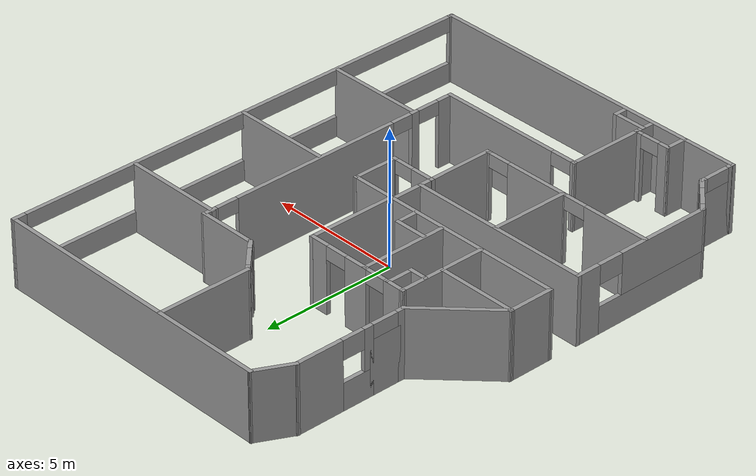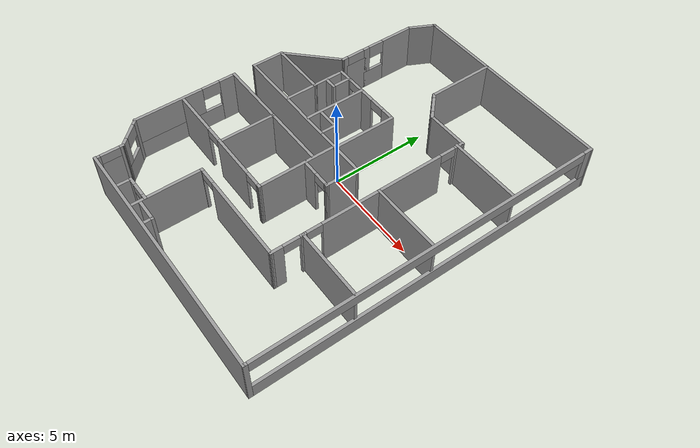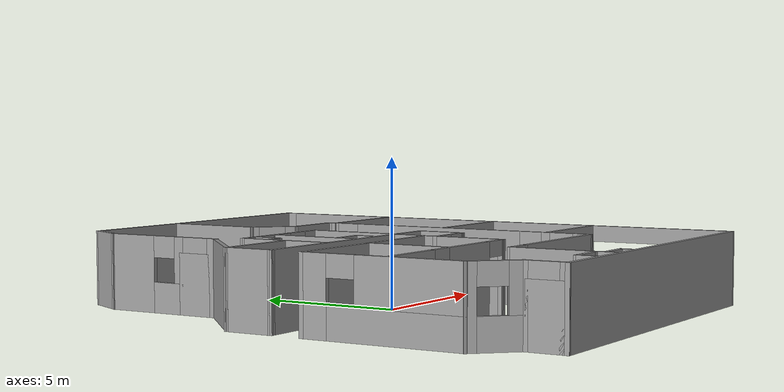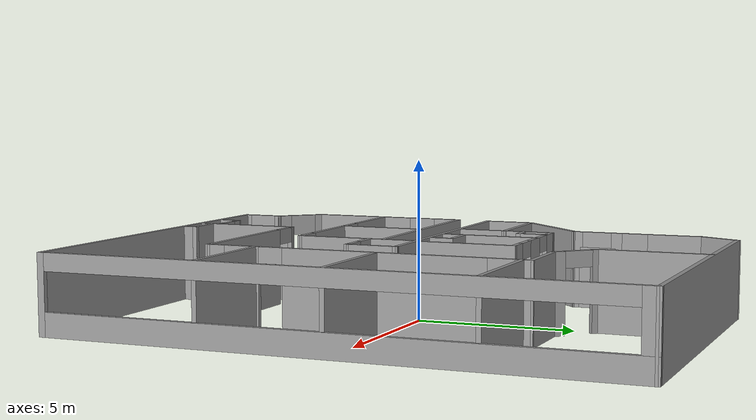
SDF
<?xml version='1.0'?>
<sdf version='1.7'>
  <model name='lake_harbour_office'>
    <link name='Wall_0'>
      <pose>0.435117 -5.60543 0 0 -0 2e-06</pose>
      <self_collide>0</self_collide>
      <enable_wind>0</enable_wind>
      <kinematic>0</kinematic>
      <visual name='Wall_0_Visual_1'>
        <pose>0.513518 0 1.25 0 -0 0</pose>
        <geometry>
          <box>
            <size>4.68067 0.15 2.5</size>
          </box>
        </geometry>
        <material>
          <script>
            <uri>file://media/materials/scripts/gazebo.material</uri>
            <name>Gazebo/Grey</name>
          </script>
          <ambient>1 1 1 1</ambient>
          <shader type='pixel'/>
        </material>
        <meta>
          <layer>0</layer>
        </meta>
        <transparency>0</transparency>
        <cast_shadows>1</cast_shadows>
      </visual>
      <visual name='Wall_0_Visual_0'>
        <pose>-2.75685 0 1.25 0 -0 0</pose>
        <geometry>
          <box>
            <size>0.194017 0.15 2.5</size>
          </box>
        </geometry>
        <material>
          <script>
            <uri>file://media/materials/scripts/gazebo.material</uri>
            <name>Gazebo/Grey</name>
          </script>
          <ambient>1 1 1 1</ambient>
          <shader type='pixel'/>
        </material>
        <meta>
          <layer>0</layer>
        </meta>
        <transparency>0</transparency>
        <cast_shadows>1</cast_shadows>
      </visual>
      <visual name='Wall_0_Visual_2'>
        <pose>-2.24333 0 2.25 0 -0 0</pose>
        <geometry>
          <box>
            <size>0.833019 0.15 0.5</size>
          </box>
        </geometry>
        <material>
          <script>
            <uri>file://media/materials/scripts/gazebo.material</uri>
            <name>Gazebo/Grey</name>
          </script>
          <ambient>1 1 1 1</ambient>
          <shader type='pixel'/>
        </material>
        <meta>
          <layer>0</layer>
        </meta>
        <transparency>0</transparency>
        <cast_shadows>1</cast_shadows>
      </visual>
      <collision name='Wall_0_Collision_1'>
        <laser_retro>0</laser_retro>
        <max_contacts>10</max_contacts>
        <pose>0.513518 0 1.25 0 -0 0</pose>
        <geometry>
          <box>
            <size>4.68067 0.15 2.5</size>
          </box>
        </geometry>
        <surface>
          <friction>
            <ode>
              <mu>1</mu>
              <mu2>1</mu2>
              <fdir1>0 0 0</fdir1>
              <slip1>0</slip1>
              <slip2>0</slip2>
            </ode>
            <torsional>
              <coefficient>1</coefficient>
              <patch_radius>0</patch_radius>
              <surface_radius>0</surface_radius>
              <use_patch_radius>1</use_patch_radius>
              <ode>
                <slip>0</slip>
              </ode>
            </torsional>
          </friction>
          <bounce>
            <restitution_coefficient>0</restitution_coefficient>
            <threshold>1e+06</threshold>
          </bounce>
          <contact>
            <collide_without_contact>0</collide_without_contact>
            <collide_without_contact_bitmask>1</collide_without_contact_bitmask>
            <collide_bitmask>1</collide_bitmask>
            <ode>
              <soft_cfm>0</soft_cfm>
              <soft_erp>0.2</soft_erp>
              <kp>1e+13</kp>
              <kd>1</kd>
              <max_vel>0.01</max_vel>
              <min_depth>0</min_depth>
            </ode>
            <bullet>
              <split_impulse>1</split_impulse>
              <split_impulse_penetration_threshold>-0.01</split_impulse_penetration_threshold>
              <soft_cfm>0</soft_cfm>
              <soft_erp>0.2</soft_erp>
              <kp>1e+13</kp>
              <kd>1</kd>
            </bullet>
          </contact>
        </surface>
      </collision>
      <collision name='Wall_0_Collision_2'>
        <laser_retro>0</laser_retro>
        <max_contacts>10</max_contacts>
        <pose>-2.24333 0 2.25 0 -0 0</pose>
        <geometry>
          <box>
            <size>0.833019 0.15 0.5</size>
          </box>
        </geometry>
        <surface>
          <friction>
            <ode>
              <mu>1</mu>
              <mu2>1</mu2>
              <fdir1>0 0 0</fdir1>
              <slip1>0</slip1>
              <slip2>0</slip2>
            </ode>
            <torsional>
              <coefficient>1</coefficient>
              <patch_radius>0</patch_radius>
              <surface_radius>0</surface_radius>
              <use_patch_radius>1</use_patch_radius>
              <ode>
                <slip>0</slip>
              </ode>
            </torsional>
          </friction>
          <bounce>
            <restitution_coefficient>0</restitution_coefficient>
            <threshold>1e+06</threshold>
          </bounce>
          <contact>
            <collide_without_contact>0</collide_without_contact>
            <collide_without_contact_bitmask>1</collide_without_contact_bitmask>
            <collide_bitmask>1</collide_bitmask>
            <ode>
              <soft_cfm>0</soft_cfm>
              <soft_erp>0.2</soft_erp>
              <kp>1e+13</kp>
              <kd>1</kd>
              <max_vel>0.01</max_vel>
              <min_depth>0</min_depth>
            </ode>
            <bullet>
              <split_impulse>1</split_impulse>
              <split_impulse_penetration_threshold>-0.01</split_impulse_penetration_threshold>
              <soft_cfm>0</soft_cfm>
              <soft_erp>0.2</soft_erp>
              <kp>1e+13</kp>
              <kd>1</kd>
            </bullet>
          </contact>
        </surface>
      </collision>
      <collision name='Wall_0_Collision_0'>
        <laser_retro>0</laser_retro>
        <max_contacts>10</max_contacts>
        <pose>-2.75685 0 1.25 0 -0 0</pose>
        <geometry>
          <box>
            <size>0.194017 0.15 2.5</size>
          </box>
        </geometry>
        <surface>
          <friction>
            <ode>
              <mu>1</mu>
              <mu2>1</mu2>
              <fdir1>0 0 0</fdir1>
              <slip1>0</slip1>
              <slip2>0</slip2>
            </ode>
            <torsional>
              <coefficient>1</coefficient>
              <patch_radius>0</patch_radius>
              <surface_radius>0</surface_radius>
              <use_patch_radius>1</use_patch_radius>
              <ode>
                <slip>0</slip>
              </ode>
            </torsional>
          </friction>
          <bounce>
            <restitution_coefficient>0</restitution_coefficient>
            <threshold>1e+06</threshold>
          </bounce>
          <contact>
            <collide_without_contact>0</collide_without_contact>
            <collide_without_contact_bitmask>1</collide_without_contact_bitmask>
            <collide_bitmask>1</collide_bitmask>
            <ode>
              <soft_cfm>0</soft_cfm>
              <soft_erp>0.2</soft_erp>
              <kp>1e+13</kp>
              <kd>1</kd>
              <max_vel>0.01</max_vel>
              <min_depth>0</min_depth>
            </ode>
            <bullet>
              <split_impulse>1</split_impulse>
              <split_impulse_penetration_threshold>-0.01</split_impulse_penetration_threshold>
              <soft_cfm>0</soft_cfm>
              <soft_erp>0.2</soft_erp>
              <kp>1e+13</kp>
              <kd>1</kd>
            </bullet>
          </contact>
        </surface>
      </collision>
    </link>
    <link name='Wall_1'>
      <pose>3.2104 -0.472625 0 0 -0 1.57149</pose>
      <self_collide>0</self_collide>
      <enable_wind>0</enable_wind>
      <kinematic>0</kinematic>
      <visual name='Wall_1_Visual_3'>
        <pose>4.9339 0 1.25 0 -0 0</pose>
        <geometry>
          <box>
            <size>0.54781 0.15 2.5</size>
          </box>
        </geometry>
        <material>
          <script>
            <uri>file://media/materials/scripts/gazebo.material</uri>
            <name>Gazebo/Grey</name>
          </script>
          <ambient>1 1 1 1</ambient>
          <shader type='pixel'/>
        </material>
        <meta>
          <layer>0</layer>
        </meta>
        <transparency>0</transparency>
        <cast_shadows>1</cast_shadows>
      </visual>
      <visual name='Wall_1_Visual_6'>
        <pose>4.25227 0 2.25 0 -0 0</pose>
        <geometry>
          <box>
            <size>0.815447 0.15 0.5</size>
          </box>
        </geometry>
        <material>
          <script>
            <uri>file://media/materials/scripts/gazebo.material</uri>
            <name>Gazebo/Grey</name>
          </script>
          <ambient>1 1 1 1</ambient>
          <shader type='pixel'/>
        </material>
        <meta>
          <layer>0</layer>
        </meta>
        <transparency>0</transparency>
        <cast_shadows>1</cast_shadows>
      </visual>
      <visual name='Wall_1_Visual_0'>
        <pose>-4.88335 0 1.25 0 -0 0</pose>
        <geometry>
          <box>
            <size>0.648917 0.15 2.5</size>
          </box>
        </geometry>
        <material>
          <script>
            <uri>file://media/materials/scripts/gazebo.material</uri>
            <name>Gazebo/Grey</name>
          </script>
          <ambient>1 1 1 1</ambient>
          <shader type='pixel'/>
        </material>
        <meta>
          <layer>0</layer>
        </meta>
        <transparency>0</transparency>
        <cast_shadows>1</cast_shadows>
      </visual>
      <visual name='Wall_1_Visual_4'>
        <pose>-4.1362 0 2.25 0 -0 0</pose>
        <geometry>
          <box>
            <size>0.845376 0.15 0.5</size>
          </box>
        </geometry>
        <material>
          <script>
            <uri>file://media/materials/scripts/gazebo.material</uri>
            <name>Gazebo/Grey</name>
          </script>
          <ambient>1 1 1 1</ambient>
          <shader type='pixel'/>
        </material>
        <meta>
          <layer>0</layer>
        </meta>
        <transparency>0</transparency>
        <cast_shadows>1</cast_shadows>
      </visual>
      <visual name='Wall_1_Visual_1'>
        <pose>-3.55701 0 1.25 0 -0 0</pose>
        <geometry>
          <box>
            <size>0.313004 0.15 2.5</size>
          </box>
        </geometry>
        <material>
          <script>
            <uri>file://media/materials/scripts/gazebo.material</uri>
            <name>Gazebo/Grey</name>
          </script>
          <ambient>1 1 1 1</ambient>
          <shader type='pixel'/>
        </material>
        <meta>
          <layer>0</layer>
        </meta>
        <transparency>0</transparency>
        <cast_shadows>1</cast_shadows>
      </visual>
      <visual name='Wall_1_Visual_5'>
        <pose>-3.00452 0 2.25 0 -0 0</pose>
        <geometry>
          <box>
            <size>0.79198 0.15 0.5</size>
          </box>
        </geometry>
        <material>
          <script>
            <uri>file://media/materials/scripts/gazebo.material</uri>
            <name>Gazebo/Grey</name>
          </script>
          <ambient>1 1 1 1</ambient>
          <shader type='pixel'/>
        </material>
        <meta>
          <layer>0</layer>
        </meta>
        <transparency>0</transparency>
        <cast_shadows>1</cast_shadows>
      </visual>
      <visual name='Wall_1_Visual_2'>
        <pose>0.61801 0 1.25 0 -0 0</pose>
        <geometry>
          <box>
            <size>6.45307 0.15 2.5</size>
          </box>
        </geometry>
        <material>
          <script>
            <uri>file://media/materials/scripts/gazebo.material</uri>
            <name>Gazebo/Grey</name>
          </script>
          <ambient>1 1 1 1</ambient>
          <shader type='pixel'/>
        </material>
        <meta>
          <layer>0</layer>
        </meta>
        <transparency>0</transparency>
        <cast_shadows>1</cast_shadows>
      </visual>
      <collision name='Wall_1_Collision_2'>
        <laser_retro>0</laser_retro>
        <max_contacts>10</max_contacts>
        <pose>0.61801 0 1.25 0 -0 0</pose>
        <geometry>
          <box>
            <size>6.45307 0.15 2.5</size>
          </box>
        </geometry>
        <surface>
          <friction>
            <ode>
              <mu>1</mu>
              <mu2>1</mu2>
              <fdir1>0 0 0</fdir1>
              <slip1>0</slip1>
              <slip2>0</slip2>
            </ode>
            <torsional>
              <coefficient>1</coefficient>
              <patch_radius>0</patch_radius>
              <surface_radius>0</surface_radius>
              <use_patch_radius>1</use_patch_radius>
              <ode>
                <slip>0</slip>
              </ode>
            </torsional>
          </friction>
          <bounce>
            <restitution_coefficient>0</restitution_coefficient>
            <threshold>1e+06</threshold>
          </bounce>
          <contact>
            <collide_without_contact>0</collide_without_contact>
            <collide_without_contact_bitmask>1</collide_without_contact_bitmask>
            <collide_bitmask>1</collide_bitmask>
            <ode>
              <soft_cfm>0</soft_cfm>
              <soft_erp>0.2</soft_erp>
              <kp>1e+13</kp>
              <kd>1</kd>
              <max_vel>0.01</max_vel>
              <min_depth>0</min_depth>
            </ode>
            <bullet>
              <split_impulse>1</split_impulse>
              <split_impulse_penetration_threshold>-0.01</split_impulse_penetration_threshold>
              <soft_cfm>0</soft_cfm>
              <soft_erp>0.2</soft_erp>
              <kp>1e+13</kp>
              <kd>1</kd>
            </bullet>
          </contact>
        </surface>
      </collision>
      <collision name='Wall_1_Collision_0'>
        <laser_retro>0</laser_retro>
        <max_contacts>10</max_contacts>
        <pose>-4.88335 0 1.25 0 -0 0</pose>
        <geometry>
          <box>
            <size>0.648917 0.15 2.5</size>
          </box>
        </geometry>
        <surface>
          <friction>
            <ode>
              <mu>1</mu>
              <mu2>1</mu2>
              <fdir1>0 0 0</fdir1>
              <slip1>0</slip1>
              <slip2>0</slip2>
            </ode>
            <torsional>
              <coefficient>1</coefficient>
              <patch_radius>0</patch_radius>
              <surface_radius>0</surface_radius>
              <use_patch_radius>1</use_patch_radius>
              <ode>
                <slip>0</slip>
              </ode>
            </torsional>
          </friction>
          <bounce>
            <restitution_coefficient>0</restitution_coefficient>
            <threshold>1e+06</threshold>
          </bounce>
          <contact>
            <collide_without_contact>0</collide_without_contact>
            <collide_without_contact_bitmask>1</collide_without_contact_bitmask>
            <collide_bitmask>1</collide_bitmask>
            <ode>
              <soft_cfm>0</soft_cfm>
              <soft_erp>0.2</soft_erp>
              <kp>1e+13</kp>
              <kd>1</kd>
              <max_vel>0.01</max_vel>
              <min_depth>0</min_depth>
            </ode>
            <bullet>
              <split_impulse>1</split_impulse>
              <split_impulse_penetration_threshold>-0.01</split_impulse_penetration_threshold>
              <soft_cfm>0</soft_cfm>
              <soft_erp>0.2</soft_erp>
              <kp>1e+13</kp>
              <kd>1</kd>
            </bullet>
          </contact>
        </surface>
      </collision>
      <collision name='Wall_1_Collision_3'>
        <laser_retro>0</laser_retro>
        <max_contacts>10</max_contacts>
        <pose>4.9339 0 1.25 0 -0 0</pose>
        <geometry>
          <box>
            <size>0.54781 0.15 2.5</size>
          </box>
        </geometry>
        <surface>
          <friction>
            <ode>
              <mu>1</mu>
              <mu2>1</mu2>
              <fdir1>0 0 0</fdir1>
              <slip1>0</slip1>
              <slip2>0</slip2>
            </ode>
            <torsional>
              <coefficient>1</coefficient>
              <patch_radius>0</patch_radius>
              <surface_radius>0</surface_radius>
              <use_patch_radius>1</use_patch_radius>
              <ode>
                <slip>0</slip>
              </ode>
            </torsional>
          </friction>
          <bounce>
            <restitution_coefficient>0</restitution_coefficient>
            <threshold>1e+06</threshold>
          </bounce>
          <contact>
            <collide_without_contact>0</collide_without_contact>
            <collide_without_contact_bitmask>1</collide_without_contact_bitmask>
            <collide_bitmask>1</collide_bitmask>
            <ode>
              <soft_cfm>0</soft_cfm>
              <soft_erp>0.2</soft_erp>
              <kp>1e+13</kp>
              <kd>1</kd>
              <max_vel>0.01</max_vel>
              <min_depth>0</min_depth>
            </ode>
            <bullet>
              <split_impulse>1</split_impulse>
              <split_impulse_penetration_threshold>-0.01</split_impulse_penetration_threshold>
              <soft_cfm>0</soft_cfm>
              <soft_erp>0.2</soft_erp>
              <kp>1e+13</kp>
              <kd>1</kd>
            </bullet>
          </contact>
        </surface>
      </collision>
      <collision name='Wall_1_Collision_6'>
        <laser_retro>0</laser_retro>
        <max_contacts>10</max_contacts>
        <pose>4.25227 0 2.25 0 -0 0</pose>
        <geometry>
          <box>
            <size>0.815447 0.15 0.5</size>
          </box>
        </geometry>
        <surface>
          <friction>
            <ode>
              <mu>1</mu>
              <mu2>1</mu2>
              <fdir1>0 0 0</fdir1>
              <slip1>0</slip1>
              <slip2>0</slip2>
            </ode>
            <torsional>
              <coefficient>1</coefficient>
              <patch_radius>0</patch_radius>
              <surface_radius>0</surface_radius>
              <use_patch_radius>1</use_patch_radius>
              <ode>
                <slip>0</slip>
              </ode>
            </torsional>
          </friction>
          <bounce>
            <restitution_coefficient>0</restitution_coefficient>
            <threshold>1e+06</threshold>
          </bounce>
          <contact>
            <collide_without_contact>0</collide_without_contact>
            <collide_without_contact_bitmask>1</collide_without_contact_bitmask>
            <collide_bitmask>1</collide_bitmask>
            <ode>
              <soft_cfm>0</soft_cfm>
              <soft_erp>0.2</soft_erp>
              <kp>1e+13</kp>
              <kd>1</kd>
              <max_vel>0.01</max_vel>
              <min_depth>0</min_depth>
            </ode>
            <bullet>
              <split_impulse>1</split_impulse>
              <split_impulse_penetration_threshold>-0.01</split_impulse_penetration_threshold>
              <soft_cfm>0</soft_cfm>
              <soft_erp>0.2</soft_erp>
              <kp>1e+13</kp>
              <kd>1</kd>
            </bullet>
          </contact>
        </surface>
      </collision>
      <collision name='Wall_1_Collision_1'>
        <laser_retro>0</laser_retro>
        <max_contacts>10</max_contacts>
        <pose>-3.55701 0 1.25 0 -0 0</pose>
        <geometry>
          <box>
            <size>0.313004 0.15 2.5</size>
          </box>
        </geometry>
        <surface>
          <friction>
            <ode>
              <mu>1</mu>
              <mu2>1</mu2>
              <fdir1>0 0 0</fdir1>
              <slip1>0</slip1>
              <slip2>0</slip2>
            </ode>
            <torsional>
              <coefficient>1</coefficient>
              <patch_radius>0</patch_radius>
              <surface_radius>0</surface_radius>
              <use_patch_radius>1</use_patch_radius>
              <ode>
                <slip>0</slip>
              </ode>
            </torsional>
          </friction>
          <bounce>
            <restitution_coefficient>0</restitution_coefficient>
            <threshold>1e+06</threshold>
          </bounce>
          <contact>
            <collide_without_contact>0</collide_without_contact>
            <collide_without_contact_bitmask>1</collide_without_contact_bitmask>
            <collide_bitmask>1</collide_bitmask>
            <ode>
              <soft_cfm>0</soft_cfm>
              <soft_erp>0.2</soft_erp>
              <kp>1e+13</kp>
              <kd>1</kd>
              <max_vel>0.01</max_vel>
              <min_depth>0</min_depth>
            </ode>
            <bullet>
              <split_impulse>1</split_impulse>
              <split_impulse_penetration_threshold>-0.01</split_impulse_penetration_threshold>
              <soft_cfm>0</soft_cfm>
              <soft_erp>0.2</soft_erp>
              <kp>1e+13</kp>
              <kd>1</kd>
            </bullet>
          </contact>
        </surface>
      </collision>
      <collision name='Wall_1_Collision_4'>
        <laser_retro>0</laser_retro>
        <max_contacts>10</max_contacts>
        <pose>-4.1362 0 2.25 0 -0 0</pose>
        <geometry>
          <box>
            <size>0.845376 0.15 0.5</size>
          </box>
        </geometry>
        <surface>
          <friction>
            <ode>
              <mu>1</mu>
              <mu2>1</mu2>
              <fdir1>0 0 0</fdir1>
              <slip1>0</slip1>
              <slip2>0</slip2>
            </ode>
            <torsional>
              <coefficient>1</coefficient>
              <patch_radius>0</patch_radius>
              <surface_radius>0</surface_radius>
              <use_patch_radius>1</use_patch_radius>
              <ode>
                <slip>0</slip>
              </ode>
            </torsional>
          </friction>
          <bounce>
            <restitution_coefficient>0</restitution_coefficient>
            <threshold>1e+06</threshold>
          </bounce>
          <contact>
            <collide_without_contact>0</collide_without_contact>
            <collide_without_contact_bitmask>1</collide_without_contact_bitmask>
            <collide_bitmask>1</collide_bitmask>
            <ode>
              <soft_cfm>0</soft_cfm>
              <soft_erp>0.2</soft_erp>
              <kp>1e+13</kp>
              <kd>1</kd>
              <max_vel>0.01</max_vel>
              <min_depth>0</min_depth>
            </ode>
            <bullet>
              <split_impulse>1</split_impulse>
              <split_impulse_penetration_threshold>-0.01</split_impulse_penetration_threshold>
              <soft_cfm>0</soft_cfm>
              <soft_erp>0.2</soft_erp>
              <kp>1e+13</kp>
              <kd>1</kd>
            </bullet>
          </contact>
        </surface>
      </collision>
      <collision name='Wall_1_Collision_5'>
        <laser_retro>0</laser_retro>
        <max_contacts>10</max_contacts>
        <pose>-3.00452 0 2.25 0 -0 0</pose>
        <geometry>
          <box>
            <size>0.79198 0.15 0.5</size>
          </box>
        </geometry>
        <surface>
          <friction>
            <ode>
              <mu>1</mu>
              <mu2>1</mu2>
              <fdir1>0 0 0</fdir1>
              <slip1>0</slip1>
              <slip2>0</slip2>
            </ode>
            <torsional>
              <coefficient>1</coefficient>
              <patch_radius>0</patch_radius>
              <surface_radius>0</surface_radius>
              <use_patch_radius>1</use_patch_radius>
              <ode>
                <slip>0</slip>
              </ode>
            </torsional>
          </friction>
          <bounce>
            <restitution_coefficient>0</restitution_coefficient>
            <threshold>1e+06</threshold>
          </bounce>
          <contact>
            <collide_without_contact>0</collide_without_contact>
            <collide_without_contact_bitmask>1</collide_without_contact_bitmask>
            <collide_bitmask>1</collide_bitmask>
            <ode>
              <soft_cfm>0</soft_cfm>
              <soft_erp>0.2</soft_erp>
              <kp>1e+13</kp>
              <kd>1</kd>
              <max_vel>0.01</max_vel>
              <min_depth>0</min_depth>
            </ode>
            <bullet>
              <split_impulse>1</split_impulse>
              <split_impulse_penetration_threshold>-0.01</split_impulse_penetration_threshold>
              <soft_cfm>0</soft_cfm>
              <soft_erp>0.2</soft_erp>
              <kp>1e+13</kp>
              <kd>1</kd>
            </bullet>
          </contact>
        </surface>
      </collision>
    </link>
    <link name='Wall_13'>
      <pose>1.45427 9.08491 0 0 -0 3.14142</pose>
      <self_collide>0</self_collide>
      <enable_wind>0</enable_wind>
      <kinematic>0</kinematic>
      <visual name='Wall_13_Visual'>
        <pose>0 0 1.25 0 -0 0</pose>
        <geometry>
          <box>
            <size>10.9751 0.15 2.5</size>
          </box>
        </geometry>
        <material>
          <script>
            <uri>file://media/materials/scripts/gazebo.material</uri>
            <name>Gazebo/Grey</name>
          </script>
          <ambient>1 1 1 1</ambient>
          <shader type='pixel'/>
        </material>
        <meta>
          <layer>0</layer>
        </meta>
        <transparency>0</transparency>
        <cast_shadows>1</cast_shadows>
      </visual>
      <collision name='Wall_13_Collision'>
        <laser_retro>0</laser_retro>
        <max_contacts>10</max_contacts>
        <pose>0 0 1.25 0 -0 0</pose>
        <geometry>
          <box>
            <size>10.9751 0.15 2.5</size>
          </box>
        </geometry>
        <surface>
          <friction>
            <ode>
              <mu>1</mu>
              <mu2>1</mu2>
              <fdir1>0 0 0</fdir1>
              <slip1>0</slip1>
              <slip2>0</slip2>
            </ode>
            <torsional>
              <coefficient>1</coefficient>
              <patch_radius>0</patch_radius>
              <surface_radius>0</surface_radius>
              <use_patch_radius>1</use_patch_radius>
              <ode>
                <slip>0</slip>
              </ode>
            </torsional>
          </friction>
          <bounce>
            <restitution_coefficient>0</restitution_coefficient>
            <threshold>1e+06</threshold>
          </bounce>
          <contact>
            <collide_without_contact>0</collide_without_contact>
            <collide_without_contact_bitmask>1</collide_without_contact_bitmask>
            <collide_bitmask>1</collide_bitmask>
            <ode>
              <soft_cfm>0</soft_cfm>
              <soft_erp>0.2</soft_erp>
              <kp>1e+13</kp>
              <kd>1</kd>
              <max_vel>0.01</max_vel>
              <min_depth>0</min_depth>
            </ode>
            <bullet>
              <split_impulse>1</split_impulse>
              <split_impulse_penetration_threshold>-0.01</split_impulse_penetration_threshold>
              <soft_cfm>0</soft_cfm>
              <soft_erp>0.2</soft_erp>
              <kp>1e+13</kp>
              <kd>1</kd>
            </bullet>
          </contact>
        </surface>
      </collision>
    </link>
    <link name='Wall_17'>
      <pose>6.85256 -0.013794 0 0 -0 1.56923</pose>
      <self_collide>0</self_collide>
      <enable_wind>0</enable_wind>
      <kinematic>0</kinematic>
      <visual name='Wall_17_Visual_1'>
        <pose>0.111402 0 0.375 0 -0 0</pose>
        <geometry>
          <box>
            <size>18.1228 0.15 0.75</size>
          </box>
        </geometry>
        <material>
          <script>
            <uri>file://media/materials/scripts/gazebo.material</uri>
            <name>Gazebo/Grey</name>
          </script>
          <ambient>1 1 1 1</ambient>
          <shader type='pixel'/>
        </material>
        <meta>
          <layer>0</layer>
        </meta>
        <transparency>0</transparency>
        <cast_shadows>1</cast_shadows>
      </visual>
      <visual name='Wall_17_Visual_3'>
        <pose>-0.139985 0 2.225 0 -0 0</pose>
        <geometry>
          <box>
            <size>17.62 0.15 0.55</size>
          </box>
        </geometry>
        <material>
          <script>
            <uri>file://media/materials/scripts/gazebo.material</uri>
            <name>Gazebo/Grey</name>
          </script>
          <ambient>1 1 1 1</ambient>
          <shader type='pixel'/>
        </material>
        <meta>
          <layer>0</layer>
        </meta>
        <transparency>0</transparency>
        <cast_shadows>1</cast_shadows>
      </visual>
      <visual name='Wall_17_Visual_2'>
        <pose>8.9214 0 1.625 0 -0 0</pose>
        <geometry>
          <box>
            <size>0.502774 0.15 1.75</size>
          </box>
        </geometry>
        <material>
          <script>
            <uri>file://media/materials/scripts/gazebo.material</uri>
            <name>Gazebo/Grey</name>
          </script>
          <ambient>1 1 1 1</ambient>
          <shader type='pixel'/>
        </material>
        <meta>
          <layer>0</layer>
        </meta>
        <transparency>0</transparency>
        <cast_shadows>1</cast_shadows>
      </visual>
      <visual name='Wall_17_Visual_0'>
        <pose>-9.06139 0 1.25 0 -0 0</pose>
        <geometry>
          <box>
            <size>0.222803 0.15 2.5</size>
          </box>
        </geometry>
        <material>
          <script>
            <uri>file://media/materials/scripts/gazebo.material</uri>
            <name>Gazebo/Grey</name>
          </script>
          <ambient>1 1 1 1</ambient>
          <shader type='pixel'/>
        </material>
        <meta>
          <layer>0</layer>
        </meta>
        <transparency>0</transparency>
        <cast_shadows>1</cast_shadows>
      </visual>
      <collision name='Wall_17_Collision_1'>
        <laser_retro>0</laser_retro>
        <max_contacts>10</max_contacts>
        <pose>0.111402 0 0.375 0 -0 0</pose>
        <geometry>
          <box>
            <size>18.1228 0.15 0.75</size>
          </box>
        </geometry>
        <surface>
          <friction>
            <ode>
              <mu>1</mu>
              <mu2>1</mu2>
              <fdir1>0 0 0</fdir1>
              <slip1>0</slip1>
              <slip2>0</slip2>
            </ode>
            <torsional>
              <coefficient>1</coefficient>
              <patch_radius>0</patch_radius>
              <surface_radius>0</surface_radius>
              <use_patch_radius>1</use_patch_radius>
              <ode>
                <slip>0</slip>
              </ode>
            </torsional>
          </friction>
          <bounce>
            <restitution_coefficient>0</restitution_coefficient>
            <threshold>1e+06</threshold>
          </bounce>
          <contact>
            <collide_without_contact>0</collide_without_contact>
            <collide_without_contact_bitmask>1</collide_without_contact_bitmask>
            <collide_bitmask>1</collide_bitmask>
            <ode>
              <soft_cfm>0</soft_cfm>
              <soft_erp>0.2</soft_erp>
              <kp>1e+13</kp>
              <kd>1</kd>
              <max_vel>0.01</max_vel>
              <min_depth>0</min_depth>
            </ode>
            <bullet>
              <split_impulse>1</split_impulse>
              <split_impulse_penetration_threshold>-0.01</split_impulse_penetration_threshold>
              <soft_cfm>0</soft_cfm>
              <soft_erp>0.2</soft_erp>
              <kp>1e+13</kp>
              <kd>1</kd>
            </bullet>
          </contact>
        </surface>
      </collision>
      <collision name='Wall_17_Collision_3'>
        <laser_retro>0</laser_retro>
        <max_contacts>10</max_contacts>
        <pose>-0.139985 0 2.225 0 -0 0</pose>
        <geometry>
          <box>
            <size>17.62 0.15 0.55</size>
          </box>
        </geometry>
        <surface>
          <friction>
            <ode>
              <mu>1</mu>
              <mu2>1</mu2>
              <fdir1>0 0 0</fdir1>
              <slip1>0</slip1>
              <slip2>0</slip2>
            </ode>
            <torsional>
              <coefficient>1</coefficient>
              <patch_radius>0</patch_radius>
              <surface_radius>0</surface_radius>
              <use_patch_radius>1</use_patch_radius>
              <ode>
                <slip>0</slip>
              </ode>
            </torsional>
          </friction>
          <bounce>
            <restitution_coefficient>0</restitution_coefficient>
            <threshold>1e+06</threshold>
          </bounce>
          <contact>
            <collide_without_contact>0</collide_without_contact>
            <collide_without_contact_bitmask>1</collide_without_contact_bitmask>
            <collide_bitmask>1</collide_bitmask>
            <ode>
              <soft_cfm>0</soft_cfm>
              <soft_erp>0.2</soft_erp>
              <kp>1e+13</kp>
              <kd>1</kd>
              <max_vel>0.01</max_vel>
              <min_depth>0</min_depth>
            </ode>
            <bullet>
              <split_impulse>1</split_impulse>
              <split_impulse_penetration_threshold>-0.01</split_impulse_penetration_threshold>
              <soft_cfm>0</soft_cfm>
              <soft_erp>0.2</soft_erp>
              <kp>1e+13</kp>
              <kd>1</kd>
            </bullet>
          </contact>
        </surface>
      </collision>
      <collision name='Wall_17_Collision_2'>
        <laser_retro>0</laser_retro>
        <max_contacts>10</max_contacts>
        <pose>8.9214 0 1.625 0 -0 0</pose>
        <geometry>
          <box>
            <size>0.502774 0.15 1.75</size>
          </box>
        </geometry>
        <surface>
          <friction>
            <ode>
              <mu>1</mu>
              <mu2>1</mu2>
              <fdir1>0 0 0</fdir1>
              <slip1>0</slip1>
              <slip2>0</slip2>
            </ode>
            <torsional>
              <coefficient>1</coefficient>
              <patch_radius>0</patch_radius>
              <surface_radius>0</surface_radius>
              <use_patch_radius>1</use_patch_radius>
              <ode>
                <slip>0</slip>
              </ode>
            </torsional>
          </friction>
          <bounce>
            <restitution_coefficient>0</restitution_coefficient>
            <threshold>1e+06</threshold>
          </bounce>
          <contact>
            <collide_without_contact>0</collide_without_contact>
            <collide_without_contact_bitmask>1</collide_without_contact_bitmask>
            <collide_bitmask>1</collide_bitmask>
            <ode>
              <soft_cfm>0</soft_cfm>
              <soft_erp>0.2</soft_erp>
              <kp>1e+13</kp>
              <kd>1</kd>
              <max_vel>0.01</max_vel>
              <min_depth>0</min_depth>
            </ode>
            <bullet>
              <split_impulse>1</split_impulse>
              <split_impulse_penetration_threshold>-0.01</split_impulse_penetration_threshold>
              <soft_cfm>0</soft_cfm>
              <soft_erp>0.2</soft_erp>
              <kp>1e+13</kp>
              <kd>1</kd>
            </bullet>
          </contact>
        </surface>
      </collision>
      <collision name='Wall_17_Collision_0'>
        <laser_retro>0</laser_retro>
        <max_contacts>10</max_contacts>
        <pose>-9.06139 0 1.25 0 -0 0</pose>
        <geometry>
          <box>
            <size>0.222803 0.15 2.5</size>
          </box>
        </geometry>
        <surface>
          <friction>
            <ode>
              <mu>1</mu>
              <mu2>1</mu2>
              <fdir1>0 0 0</fdir1>
              <slip1>0</slip1>
              <slip2>0</slip2>
            </ode>
            <torsional>
              <coefficient>1</coefficient>
              <patch_radius>0</patch_radius>
              <surface_radius>0</surface_radius>
              <use_patch_radius>1</use_patch_radius>
              <ode>
                <slip>0</slip>
              </ode>
            </torsional>
          </friction>
          <bounce>
            <restitution_coefficient>0</restitution_coefficient>
            <threshold>1e+06</threshold>
          </bounce>
          <contact>
            <collide_without_contact>0</collide_without_contact>
            <collide_without_contact_bitmask>1</collide_without_contact_bitmask>
            <collide_bitmask>1</collide_bitmask>
            <ode>
              <soft_cfm>0</soft_cfm>
              <soft_erp>0.2</soft_erp>
              <kp>1e+13</kp>
              <kd>1</kd>
              <max_vel>0.01</max_vel>
              <min_depth>0</min_depth>
            </ode>
            <bullet>
              <split_impulse>1</split_impulse>
              <split_impulse_penetration_threshold>-0.01</split_impulse_penetration_threshold>
              <soft_cfm>0</soft_cfm>
              <soft_erp>0.2</soft_erp>
              <kp>1e+13</kp>
              <kd>1</kd>
            </bullet>
          </contact>
        </surface>
      </collision>
    </link>
    <link name='Wall_19'>
      <pose>5.00431 -4.0195 0 0 -0 0</pose>
      <self_collide>0</self_collide>
      <enable_wind>0</enable_wind>
      <kinematic>0</kinematic>
      <visual name='Wall_19_Visual'>
        <pose>0 0 1.25 0 -0 0</pose>
        <geometry>
          <box>
            <size>3.67 0.15 2.5</size>
          </box>
        </geometry>
        <material>
          <script>
            <uri>file://media/materials/scripts/gazebo.material</uri>
            <name>Gazebo/Grey</name>
          </script>
          <ambient>1 1 1 1</ambient>
          <shader type='pixel'/>
        </material>
        <meta>
          <layer>0</layer>
        </meta>
        <transparency>0</transparency>
        <cast_shadows>1</cast_shadows>
      </visual>
      <collision name='Wall_19_Collision'>
        <laser_retro>0</laser_retro>
        <max_contacts>10</max_contacts>
        <pose>0 0 1.25 0 -0 0</pose>
        <geometry>
          <box>
            <size>3.67 0.15 2.5</size>
          </box>
        </geometry>
        <surface>
          <friction>
            <ode>
              <mu>1</mu>
              <mu2>1</mu2>
              <fdir1>0 0 0</fdir1>
              <slip1>0</slip1>
              <slip2>0</slip2>
            </ode>
            <torsional>
              <coefficient>1</coefficient>
              <patch_radius>0</patch_radius>
              <surface_radius>0</surface_radius>
              <use_patch_radius>1</use_patch_radius>
              <ode>
                <slip>0</slip>
              </ode>
            </torsional>
          </friction>
          <bounce>
            <restitution_coefficient>0</restitution_coefficient>
            <threshold>1e+06</threshold>
          </bounce>
          <contact>
            <collide_without_contact>0</collide_without_contact>
            <collide_without_contact_bitmask>1</collide_without_contact_bitmask>
            <collide_bitmask>1</collide_bitmask>
            <ode>
              <soft_cfm>0</soft_cfm>
              <soft_erp>0.2</soft_erp>
              <kp>1e+13</kp>
              <kd>1</kd>
              <max_vel>0.01</max_vel>
              <min_depth>0</min_depth>
            </ode>
            <bullet>
              <split_impulse>1</split_impulse>
              <split_impulse_penetration_threshold>-0.01</split_impulse_penetration_threshold>
              <soft_cfm>0</soft_cfm>
              <soft_erp>0.2</soft_erp>
              <kp>1e+13</kp>
              <kd>1</kd>
            </bullet>
          </contact>
        </surface>
      </collision>
    </link>
    <link name='Wall_24'>
      <pose>-2.34637 -7.35192 0 0 0 -1.57231</pose>
      <self_collide>0</self_collide>
      <enable_wind>0</enable_wind>
      <kinematic>0</kinematic>
      <visual name='Wall_24_Visual'>
        <pose>0 0 1.25 0 -0 0</pose>
        <geometry>
          <box>
            <size>3.64297 0.15 2.5</size>
          </box>
        </geometry>
        <material>
          <script>
            <uri>file://media/materials/scripts/gazebo.material</uri>
            <name>Gazebo/Grey</name>
          </script>
          <ambient>1 1 1 1</ambient>
          <shader type='pixel'/>
        </material>
        <meta>
          <layer>0</layer>
        </meta>
        <transparency>0</transparency>
        <cast_shadows>1</cast_shadows>
      </visual>
      <collision name='Wall_24_Collision'>
        <laser_retro>0</laser_retro>
        <max_contacts>10</max_contacts>
        <pose>0 0 1.25 0 -0 0</pose>
        <geometry>
          <box>
            <size>3.64297 0.15 2.5</size>
          </box>
        </geometry>
        <surface>
          <friction>
            <ode>
              <mu>1</mu>
              <mu2>1</mu2>
              <fdir1>0 0 0</fdir1>
              <slip1>0</slip1>
              <slip2>0</slip2>
            </ode>
            <torsional>
              <coefficient>1</coefficient>
              <patch_radius>0</patch_radius>
              <surface_radius>0</surface_radius>
              <use_patch_radius>1</use_patch_radius>
              <ode>
                <slip>0</slip>
              </ode>
            </torsional>
          </friction>
          <bounce>
            <restitution_coefficient>0</restitution_coefficient>
            <threshold>1e+06</threshold>
          </bounce>
          <contact>
            <collide_without_contact>0</collide_without_contact>
            <collide_without_contact_bitmask>1</collide_without_contact_bitmask>
            <collide_bitmask>1</collide_bitmask>
            <ode>
              <soft_cfm>0</soft_cfm>
              <soft_erp>0.2</soft_erp>
              <kp>1e+13</kp>
              <kd>1</kd>
              <max_vel>0.01</max_vel>
              <min_depth>0</min_depth>
            </ode>
            <bullet>
              <split_impulse>1</split_impulse>
              <split_impulse_penetration_threshold>-0.01</split_impulse_penetration_threshold>
              <soft_cfm>0</soft_cfm>
              <soft_erp>0.2</soft_erp>
              <kp>1e+13</kp>
              <kd>1</kd>
            </bullet>
          </contact>
        </surface>
      </collision>
    </link>
    <link name='Wall_26'>
      <pose>-4.26687 8.47883 0 0 0 -2.04113</pose>
      <self_collide>0</self_collide>
      <enable_wind>0</enable_wind>
      <kinematic>0</kinematic>
      <visual name='Wall_26_Visual'>
        <pose>0 0 1.25 0 -0 0</pose>
        <geometry>
          <box>
            <size>1.5119 0.15 2.5</size>
          </box>
        </geometry>
        <material>
          <script>
            <uri>file://media/materials/scripts/gazebo.material</uri>
            <name>Gazebo/Grey</name>
          </script>
          <ambient>1 1 1 1</ambient>
          <shader type='pixel'/>
        </material>
        <meta>
          <layer>0</layer>
        </meta>
        <transparency>0</transparency>
        <cast_shadows>1</cast_shadows>
      </visual>
      <collision name='Wall_26_Collision'>
        <laser_retro>0</laser_retro>
        <max_contacts>10</max_contacts>
        <pose>0 0 1.25 0 -0 0</pose>
        <geometry>
          <box>
            <size>1.5119 0.15 2.5</size>
          </box>
        </geometry>
        <surface>
          <friction>
            <ode>
              <mu>1</mu>
              <mu2>1</mu2>
              <fdir1>0 0 0</fdir1>
              <slip1>0</slip1>
              <slip2>0</slip2>
            </ode>
            <torsional>
              <coefficient>1</coefficient>
              <patch_radius>0</patch_radius>
              <surface_radius>0</surface_radius>
              <use_patch_radius>1</use_patch_radius>
              <ode>
                <slip>0</slip>
              </ode>
            </torsional>
          </friction>
          <bounce>
            <restitution_coefficient>0</restitution_coefficient>
            <threshold>1e+06</threshold>
          </bounce>
          <contact>
            <collide_without_contact>0</collide_without_contact>
            <collide_without_contact_bitmask>1</collide_without_contact_bitmask>
            <collide_bitmask>1</collide_bitmask>
            <ode>
              <soft_cfm>0</soft_cfm>
              <soft_erp>0.2</soft_erp>
              <kp>1e+13</kp>
              <kd>1</kd>
              <max_vel>0.01</max_vel>
              <min_depth>0</min_depth>
            </ode>
            <bullet>
              <split_impulse>1</split_impulse>
              <split_impulse_penetration_threshold>-0.01</split_impulse_penetration_threshold>
              <soft_cfm>0</soft_cfm>
              <soft_erp>0.2</soft_erp>
              <kp>1e+13</kp>
              <kd>1</kd>
            </bullet>
          </contact>
        </surface>
      </collision>
    </link>
    <link name='Wall_28'>
      <pose>-4.57547 5.77869 0 0 0 -1.5708</pose>
      <self_collide>0</self_collide>
      <enable_wind>0</enable_wind>
      <kinematic>0</kinematic>
      <gravity>1</gravity>
      <inertial>
        <mass>1</mass>
        <pose>0 0 0 0 -0 0</pose>
        <inertia>
          <ixx>1</ixx>
          <ixy>0</ixy>
          <ixz>0</ixz>
          <iyy>1</iyy>
          <iyz>0</iyz>
          <izz>1</izz>
        </inertia>
      </inertial>
      <visual name='Wall_28_Visual_5'>
        <pose>1.32226 0 2.25 0 -0 0</pose>
        <geometry>
          <box>
            <size>0.960993 0.15 0.5</size>
          </box>
        </geometry>
        <material>
          <script>
            <uri>file://media/materials/scripts/gazebo.material</uri>
            <name>Gazebo/Grey</name>
          </script>
          <ambient>1 1 1 1</ambient>
          <shader type='pixel'>
            <normal_map>__default__</normal_map>
          </shader>
          <diffuse>0.7 0.7 0.7 1</diffuse>
          <specular>0.01 0.01 0.01 1</specular>
          <emissive>0 0 0 1</emissive>
        </material>
        <meta>
          <layer>0</layer>
        </meta>
        <transparency>0</transparency>
        <cast_shadows>1</cast_shadows>
      </visual>
      <visual name='Wall_28_Visual_4'>
        <pose>0.066565 0 2.15 0 -0 0</pose>
        <geometry>
          <box>
            <size>0.840547 0.15 0.7</size>
          </box>
        </geometry>
        <material>
          <script>
            <uri>file://media/materials/scripts/gazebo.material</uri>
            <name>Gazebo/Grey</name>
          </script>
          <ambient>1 1 1 1</ambient>
          <shader type='pixel'>
            <normal_map>__default__</normal_map>
          </shader>
          <diffuse>0.7 0.7 0.7 1</diffuse>
          <specular>0.01 0.01 0.01 1</specular>
          <emissive>0 0 0 1</emissive>
        </material>
        <meta>
          <layer>0</layer>
        </meta>
        <transparency>0</transparency>
        <cast_shadows>1</cast_shadows>
      </visual>
      <visual name='Wall_28_Visual_0'>
        <pose>-1.26092 0 1.25 0 -0 0</pose>
        <geometry>
          <box>
            <size>1.81443 0.15 2.5</size>
          </box>
        </geometry>
        <material>
          <script>
            <uri>file://media/materials/scripts/gazebo.material</uri>
            <name>Gazebo/Grey</name>
          </script>
          <ambient>1 1 1 1</ambient>
          <shader type='pixel'>
            <normal_map>__default__</normal_map>
          </shader>
          <diffuse>0.7 0.7 0.7 1</diffuse>
          <specular>0.01 0.01 0.01 1</specular>
          <emissive>0 0 0 1</emissive>
        </material>
        <meta>
          <layer>0</layer>
        </meta>
        <transparency>0</transparency>
        <cast_shadows>1</cast_shadows>
      </visual>
      <visual name='Wall_28_Visual_2'>
        <pose>0.244026 0 0.5 0 -0 0</pose>
        <geometry>
          <box>
            <size>1.19547 0.15 1</size>
          </box>
        </geometry>
        <material>
          <script>
            <uri>file://media/materials/scripts/gazebo.material</uri>
            <name>Gazebo/Grey</name>
          </script>
          <ambient>1 1 1 1</ambient>
          <shader type='pixel'>
            <normal_map>__default__</normal_map>
          </shader>
          <diffuse>0.7 0.7 0.7 1</diffuse>
          <specular>0.01 0.01 0.01 1</specular>
          <emissive>0 0 0 1</emissive>
        </material>
        <meta>
          <layer>0</layer>
        </meta>
        <transparency>0</transparency>
        <cast_shadows>1</cast_shadows>
      </visual>
      <visual name='Wall_28_Visual_3'>
        <pose>0.6643 0 1.75 0 -0 0</pose>
        <geometry>
          <box>
            <size>0.354924 0.15 1.5</size>
          </box>
        </geometry>
        <material>
          <script>
            <uri>file://media/materials/scripts/gazebo.material</uri>
            <name>Gazebo/Grey</name>
          </script>
          <ambient>1 1 1 1</ambient>
          <shader type='pixel'>
            <normal_map>__default__</normal_map>
          </shader>
          <diffuse>0.7 0.7 0.7 1</diffuse>
          <specular>0.01 0.01 0.01 1</specular>
          <emissive>0 0 0 1</emissive>
        </material>
        <meta>
          <layer>0</layer>
        </meta>
        <transparency>0</transparency>
        <cast_shadows>1</cast_shadows>
      </visual>
      <visual name='Wall_28_Visual_1'>
        <pose>1.98545 0 1.25 0 -0 0</pose>
        <geometry>
          <box>
            <size>0.365381 0.15 2.5</size>
          </box>
        </geometry>
        <material>
          <script>
            <uri>file://media/materials/scripts/gazebo.material</uri>
            <name>Gazebo/Grey</name>
          </script>
          <ambient>1 1 1 1</ambient>
          <shader type='pixel'>
            <normal_map>__default__</normal_map>
          </shader>
          <diffuse>0.7 0.7 0.7 1</diffuse>
          <specular>0.01 0.01 0.01 1</specular>
          <emissive>0 0 0 1</emissive>
        </material>
        <meta>
          <layer>0</layer>
        </meta>
        <transparency>0</transparency>
        <cast_shadows>1</cast_shadows>
      </visual>
      <visual name='ModelPreview_5::Wall_28::visual_6'>
        <pose>1.3 0 1 0 -0 0</pose>
        <geometry>
          <box>
            <size>1.2 0.15 2</size>
          </box>
        </geometry>
        <material>
          <script>
            <uri>file://media/materials/scripts/gazebo.material</uri>
            <name>Gazebo/Grey</name>
          </script>
          <ambient>1 1 1 1</ambient>
          <shader type='pixel'>
            <normal_map>__default__</normal_map>
          </shader>
          <diffuse>0.7 0.7 0.7 1</diffuse>
          <specular>0.01 0.01 0.01 1</specular>
          <emissive>0 0 0 1</emissive>
        </material>
        <meta>
          <layer>0</layer>
        </meta>
        <transparency>0</transparency>
        <cast_shadows>1</cast_shadows>
      </visual>
      <collision name='Wall_28_Collision_5'>
        <laser_retro>0</laser_retro>
        <max_contacts>10</max_contacts>
        <pose>1.32226 0 2.25 0 -0 0</pose>
        <geometry>
          <box>
            <size>0.960993 0.15 0.5</size>
          </box>
        </geometry>
        <surface>
          <friction>
            <ode>
              <mu>1</mu>
              <mu2>1</mu2>
              <fdir1>0 0 0</fdir1>
              <slip1>0</slip1>
              <slip2>0</slip2>
            </ode>
            <torsional>
              <coefficient>1</coefficient>
              <patch_radius>0</patch_radius>
              <surface_radius>0</surface_radius>
              <use_patch_radius>1</use_patch_radius>
              <ode>
                <slip>0</slip>
              </ode>
            </torsional>
          </friction>
          <bounce>
            <restitution_coefficient>0</restitution_coefficient>
            <threshold>1e+06</threshold>
          </bounce>
          <contact>
            <collide_without_contact>0</collide_without_contact>
            <collide_without_contact_bitmask>1</collide_without_contact_bitmask>
            <collide_bitmask>1</collide_bitmask>
            <ode>
              <soft_cfm>0</soft_cfm>
              <soft_erp>0.2</soft_erp>
              <kp>1e+13</kp>
              <kd>1</kd>
              <max_vel>0.01</max_vel>
              <min_depth>0</min_depth>
            </ode>
            <bullet>
              <split_impulse>1</split_impulse>
              <split_impulse_penetration_threshold>-0.01</split_impulse_penetration_threshold>
              <soft_cfm>0</soft_cfm>
              <soft_erp>0.2</soft_erp>
              <kp>1e+13</kp>
              <kd>1</kd>
            </bullet>
          </contact>
        </surface>
      </collision>
      <collision name='Wall_28_Collision_4'>
        <laser_retro>0</laser_retro>
        <max_contacts>10</max_contacts>
        <pose>0.066565 0 2.15 0 -0 0</pose>
        <geometry>
          <box>
            <size>0.840547 0.15 0.7</size>
          </box>
        </geometry>
        <surface>
          <friction>
            <ode>
              <mu>1</mu>
              <mu2>1</mu2>
              <fdir1>0 0 0</fdir1>
              <slip1>0</slip1>
              <slip2>0</slip2>
            </ode>
            <torsional>
              <coefficient>1</coefficient>
              <patch_radius>0</patch_radius>
              <surface_radius>0</surface_radius>
              <use_patch_radius>1</use_patch_radius>
              <ode>
                <slip>0</slip>
              </ode>
            </torsional>
          </friction>
          <bounce>
            <restitution_coefficient>0</restitution_coefficient>
            <threshold>1e+06</threshold>
          </bounce>
          <contact>
            <collide_without_contact>0</collide_without_contact>
            <collide_without_contact_bitmask>1</collide_without_contact_bitmask>
            <collide_bitmask>1</collide_bitmask>
            <ode>
              <soft_cfm>0</soft_cfm>
              <soft_erp>0.2</soft_erp>
              <kp>1e+13</kp>
              <kd>1</kd>
              <max_vel>0.01</max_vel>
              <min_depth>0</min_depth>
            </ode>
            <bullet>
              <split_impulse>1</split_impulse>
              <split_impulse_penetration_threshold>-0.01</split_impulse_penetration_threshold>
              <soft_cfm>0</soft_cfm>
              <soft_erp>0.2</soft_erp>
              <kp>1e+13</kp>
              <kd>1</kd>
            </bullet>
          </contact>
        </surface>
      </collision>
      <collision name='Wall_28_Collision_2'>
        <laser_retro>0</laser_retro>
        <max_contacts>10</max_contacts>
        <pose>0.244026 0 0.5 0 -0 0</pose>
        <geometry>
          <box>
            <size>1.19547 0.15 1</size>
          </box>
        </geometry>
        <surface>
          <friction>
            <ode>
              <mu>1</mu>
              <mu2>1</mu2>
              <fdir1>0 0 0</fdir1>
              <slip1>0</slip1>
              <slip2>0</slip2>
            </ode>
            <torsional>
              <coefficient>1</coefficient>
              <patch_radius>0</patch_radius>
              <surface_radius>0</surface_radius>
              <use_patch_radius>1</use_patch_radius>
              <ode>
                <slip>0</slip>
              </ode>
            </torsional>
          </friction>
          <bounce>
            <restitution_coefficient>0</restitution_coefficient>
            <threshold>1e+06</threshold>
          </bounce>
          <contact>
            <collide_without_contact>0</collide_without_contact>
            <collide_without_contact_bitmask>1</collide_without_contact_bitmask>
            <collide_bitmask>1</collide_bitmask>
            <ode>
              <soft_cfm>0</soft_cfm>
              <soft_erp>0.2</soft_erp>
              <kp>1e+13</kp>
              <kd>1</kd>
              <max_vel>0.01</max_vel>
              <min_depth>0</min_depth>
            </ode>
            <bullet>
              <split_impulse>1</split_impulse>
              <split_impulse_penetration_threshold>-0.01</split_impulse_penetration_threshold>
              <soft_cfm>0</soft_cfm>
              <soft_erp>0.2</soft_erp>
              <kp>1e+13</kp>
              <kd>1</kd>
            </bullet>
          </contact>
        </surface>
      </collision>
      <collision name='collision_6'>
        <laser_retro>0</laser_retro>
        <max_contacts>10</max_contacts>
        <pose>1.3 0 1 0 -0 0</pose>
        <geometry>
          <box>
            <size>1.2 0.15 2</size>
          </box>
        </geometry>
        <surface>
          <friction>
            <ode>
              <mu>1</mu>
              <mu2>1</mu2>
              <fdir1>0 0 0</fdir1>
              <slip1>0</slip1>
              <slip2>0</slip2>
            </ode>
            <torsional>
              <coefficient>1</coefficient>
              <patch_radius>0</patch_radius>
              <surface_radius>0</surface_radius>
              <use_patch_radius>1</use_patch_radius>
              <ode>
                <slip>0</slip>
              </ode>
            </torsional>
          </friction>
          <bounce>
            <restitution_coefficient>0</restitution_coefficient>
            <threshold>1e+06</threshold>
          </bounce>
          <contact>
            <collide_without_contact>0</collide_without_contact>
            <collide_without_contact_bitmask>1</collide_without_contact_bitmask>
            <collide_bitmask>1</collide_bitmask>
            <ode>
              <soft_cfm>0</soft_cfm>
              <soft_erp>0.2</soft_erp>
              <kp>1e+13</kp>
              <kd>1</kd>
              <max_vel>0.01</max_vel>
              <min_depth>0</min_depth>
            </ode>
            <bullet>
              <split_impulse>1</split_impulse>
              <split_impulse_penetration_threshold>-0.01</split_impulse_penetration_threshold>
              <soft_cfm>0</soft_cfm>
              <soft_erp>0.2</soft_erp>
              <kp>1e+13</kp>
              <kd>1</kd>
            </bullet>
          </contact>
        </surface>
      </collision>
      <collision name='Wall_28_Collision_3'>
        <laser_retro>0</laser_retro>
        <max_contacts>10</max_contacts>
        <pose>0.6643 0 1.75 0 -0 0</pose>
        <geometry>
          <box>
            <size>0.354924 0.15 1.5</size>
          </box>
        </geometry>
        <surface>
          <friction>
            <ode>
              <mu>1</mu>
              <mu2>1</mu2>
              <fdir1>0 0 0</fdir1>
              <slip1>0</slip1>
              <slip2>0</slip2>
            </ode>
            <torsional>
              <coefficient>1</coefficient>
              <patch_radius>0</patch_radius>
              <surface_radius>0</surface_radius>
              <use_patch_radius>1</use_patch_radius>
              <ode>
                <slip>0</slip>
              </ode>
            </torsional>
          </friction>
          <bounce>
            <restitution_coefficient>0</restitution_coefficient>
            <threshold>1e+06</threshold>
          </bounce>
          <contact>
            <collide_without_contact>0</collide_without_contact>
            <collide_without_contact_bitmask>1</collide_without_contact_bitmask>
            <collide_bitmask>1</collide_bitmask>
            <ode>
              <soft_cfm>0</soft_cfm>
              <soft_erp>0.2</soft_erp>
              <kp>1e+13</kp>
              <kd>1</kd>
              <max_vel>0.01</max_vel>
              <min_depth>0</min_depth>
            </ode>
            <bullet>
              <split_impulse>1</split_impulse>
              <split_impulse_penetration_threshold>-0.01</split_impulse_penetration_threshold>
              <soft_cfm>0</soft_cfm>
              <soft_erp>0.2</soft_erp>
              <kp>1e+13</kp>
              <kd>1</kd>
            </bullet>
          </contact>
        </surface>
      </collision>
      <collision name='Wall_28_Collision_1'>
        <laser_retro>0</laser_retro>
        <max_contacts>10</max_contacts>
        <pose>1.98545 0 1.25 0 -0 0</pose>
        <geometry>
          <box>
            <size>0.365381 0.15 2.5</size>
          </box>
        </geometry>
        <surface>
          <friction>
            <ode>
              <mu>1</mu>
              <mu2>1</mu2>
              <fdir1>0 0 0</fdir1>
              <slip1>0</slip1>
              <slip2>0</slip2>
            </ode>
            <torsional>
              <coefficient>1</coefficient>
              <patch_radius>0</patch_radius>
              <surface_radius>0</surface_radius>
              <use_patch_radius>1</use_patch_radius>
              <ode>
                <slip>0</slip>
              </ode>
            </torsional>
          </friction>
          <bounce>
            <restitution_coefficient>0</restitution_coefficient>
            <threshold>1e+06</threshold>
          </bounce>
          <contact>
            <collide_without_contact>0</collide_without_contact>
            <collide_without_contact_bitmask>1</collide_without_contact_bitmask>
            <collide_bitmask>1</collide_bitmask>
            <ode>
              <soft_cfm>0</soft_cfm>
              <soft_erp>0.2</soft_erp>
              <kp>1e+13</kp>
              <kd>1</kd>
              <max_vel>0.01</max_vel>
              <min_depth>0</min_depth>
            </ode>
            <bullet>
              <split_impulse>1</split_impulse>
              <split_impulse_penetration_threshold>-0.01</split_impulse_penetration_threshold>
              <soft_cfm>0</soft_cfm>
              <soft_erp>0.2</soft_erp>
              <kp>1e+13</kp>
              <kd>1</kd>
            </bullet>
          </contact>
        </surface>
      </collision>
      <collision name='Wall_28_Collision_0'>
        <laser_retro>0</laser_retro>
        <max_contacts>10</max_contacts>
        <pose>-1.26092 0 1.25 0 -0 0</pose>
        <geometry>
          <box>
            <size>1.81443 0.15 2.5</size>
          </box>
        </geometry>
        <surface>
          <friction>
            <ode>
              <mu>1</mu>
              <mu2>1</mu2>
              <fdir1>0 0 0</fdir1>
              <slip1>0</slip1>
              <slip2>0</slip2>
            </ode>
            <torsional>
              <coefficient>1</coefficient>
              <patch_radius>0</patch_radius>
              <surface_radius>0</surface_radius>
              <use_patch_radius>1</use_patch_radius>
              <ode>
                <slip>0</slip>
              </ode>
            </torsional>
          </friction>
          <bounce>
            <restitution_coefficient>0</restitution_coefficient>
            <threshold>1e+06</threshold>
          </bounce>
          <contact>
            <collide_without_contact>0</collide_without_contact>
            <collide_without_contact_bitmask>1</collide_without_contact_bitmask>
            <collide_bitmask>1</collide_bitmask>
            <ode>
              <soft_cfm>0</soft_cfm>
              <soft_erp>0.2</soft_erp>
              <kp>1e+13</kp>
              <kd>1</kd>
              <max_vel>0.01</max_vel>
              <min_depth>0</min_depth>
            </ode>
            <bullet>
              <split_impulse>1</split_impulse>
              <split_impulse_penetration_threshold>-0.01</split_impulse_penetration_threshold>
              <soft_cfm>0</soft_cfm>
              <soft_erp>0.2</soft_erp>
              <kp>1e+13</kp>
              <kd>1</kd>
            </bullet>
          </contact>
        </surface>
      </collision>
    </link>
    <link name='Wall_30'>
      <pose>-5.6836 2.58621 0 0 0 -2.36018</pose>
      <self_collide>0</self_collide>
      <enable_wind>0</enable_wind>
      <kinematic>0</kinematic>
      <visual name='Wall_30_Visual'>
        <pose>0 0 1.25 0 -0 0</pose>
        <geometry>
          <box>
            <size>3.27185 0.15 2.5</size>
          </box>
        </geometry>
        <material>
          <script>
            <uri>file://media/materials/scripts/gazebo.material</uri>
            <name>Gazebo/Grey</name>
          </script>
          <ambient>1 1 1 1</ambient>
          <shader type='pixel'/>
        </material>
        <meta>
          <layer>0</layer>
        </meta>
        <transparency>0</transparency>
        <cast_shadows>1</cast_shadows>
      </visual>
      <collision name='Wall_30_Collision'>
        <laser_retro>0</laser_retro>
        <max_contacts>10</max_contacts>
        <pose>0 0 1.25 0 -0 0</pose>
        <geometry>
          <box>
            <size>3.27185 0.15 2.5</size>
          </box>
        </geometry>
        <surface>
          <friction>
            <ode>
              <mu>1</mu>
              <mu2>1</mu2>
              <fdir1>0 0 0</fdir1>
              <slip1>0</slip1>
              <slip2>0</slip2>
            </ode>
            <torsional>
              <coefficient>1</coefficient>
              <patch_radius>0</patch_radius>
              <surface_radius>0</surface_radius>
              <use_patch_radius>1</use_patch_radius>
              <ode>
                <slip>0</slip>
              </ode>
            </torsional>
          </friction>
          <bounce>
            <restitution_coefficient>0</restitution_coefficient>
            <threshold>1e+06</threshold>
          </bounce>
          <contact>
            <collide_without_contact>0</collide_without_contact>
            <collide_without_contact_bitmask>1</collide_without_contact_bitmask>
            <collide_bitmask>1</collide_bitmask>
            <ode>
              <soft_cfm>0</soft_cfm>
              <soft_erp>0.2</soft_erp>
              <kp>1e+13</kp>
              <kd>1</kd>
              <max_vel>0.01</max_vel>
              <min_depth>0</min_depth>
            </ode>
            <bullet>
              <split_impulse>1</split_impulse>
              <split_impulse_penetration_threshold>-0.01</split_impulse_penetration_threshold>
              <soft_cfm>0</soft_cfm>
              <soft_erp>0.2</soft_erp>
              <kp>1e+13</kp>
              <kd>1</kd>
            </bullet>
          </contact>
        </surface>
      </collision>
    </link>
    <link name='Wall_32'>
      <pose>-6.80053 0.686876 0 0 0 -1.5708</pose>
      <self_collide>0</self_collide>
      <enable_wind>0</enable_wind>
      <kinematic>0</kinematic>
      <visual name='Wall_32_Visual'>
        <pose>0 0 1.25 0 -0 0</pose>
        <geometry>
          <box>
            <size>1.75 0.15 2.5</size>
          </box>
        </geometry>
        <material>
          <script>
            <uri>file://media/materials/scripts/gazebo.material</uri>
            <name>Gazebo/Grey</name>
          </script>
          <ambient>1 1 1 1</ambient>
          <shader type='pixel'/>
        </material>
        <meta>
          <layer>0</layer>
        </meta>
        <transparency>0</transparency>
        <cast_shadows>1</cast_shadows>
      </visual>
      <collision name='Wall_32_Collision'>
        <laser_retro>0</laser_retro>
        <max_contacts>10</max_contacts>
        <pose>0 0 1.25 0 -0 0</pose>
        <geometry>
          <box>
            <size>1.75 0.15 2.5</size>
          </box>
        </geometry>
        <surface>
          <friction>
            <ode>
              <mu>1</mu>
              <mu2>1</mu2>
              <fdir1>0 0 0</fdir1>
              <slip1>0</slip1>
              <slip2>0</slip2>
            </ode>
            <torsional>
              <coefficient>1</coefficient>
              <patch_radius>0</patch_radius>
              <surface_radius>0</surface_radius>
              <use_patch_radius>1</use_patch_radius>
              <ode>
                <slip>0</slip>
              </ode>
            </torsional>
          </friction>
          <bounce>
            <restitution_coefficient>0</restitution_coefficient>
            <threshold>1e+06</threshold>
          </bounce>
          <contact>
            <collide_without_contact>0</collide_without_contact>
            <collide_without_contact_bitmask>1</collide_without_contact_bitmask>
            <collide_bitmask>1</collide_bitmask>
            <ode>
              <soft_cfm>0</soft_cfm>
              <soft_erp>0.2</soft_erp>
              <kp>1e+13</kp>
              <kd>1</kd>
              <max_vel>0.01</max_vel>
              <min_depth>0</min_depth>
            </ode>
            <bullet>
              <split_impulse>1</split_impulse>
              <split_impulse_penetration_threshold>-0.01</split_impulse_penetration_threshold>
              <soft_cfm>0</soft_cfm>
              <soft_erp>0.2</soft_erp>
              <kp>1e+13</kp>
              <kd>1</kd>
            </bullet>
          </contact>
        </surface>
      </collision>
    </link>
    <link name='Wall_34'>
      <pose>-2.59189 -0.111503 0 0 -0 0.000385</pose>
      <self_collide>0</self_collide>
      <enable_wind>0</enable_wind>
      <kinematic>0</kinematic>
      <visual name='Wall_34_Visual'>
        <pose>0 0 1.25 0 -0 0</pose>
        <geometry>
          <box>
            <size>8.56728 0.15 2.5</size>
          </box>
        </geometry>
        <material>
          <script>
            <uri>file://media/materials/scripts/gazebo.material</uri>
            <name>Gazebo/Grey</name>
          </script>
          <ambient>1 1 1 1</ambient>
          <shader type='pixel'/>
        </material>
        <meta>
          <layer>0</layer>
        </meta>
        <transparency>0</transparency>
        <cast_shadows>1</cast_shadows>
      </visual>
      <collision name='Wall_34_Collision'>
        <laser_retro>0</laser_retro>
        <max_contacts>10</max_contacts>
        <pose>0 0 1.25 0 -0 0</pose>
        <geometry>
          <box>
            <size>8.56728 0.15 2.5</size>
          </box>
        </geometry>
        <surface>
          <friction>
            <ode>
              <mu>1</mu>
              <mu2>1</mu2>
              <fdir1>0 0 0</fdir1>
              <slip1>0</slip1>
              <slip2>0</slip2>
            </ode>
            <torsional>
              <coefficient>1</coefficient>
              <patch_radius>0</patch_radius>
              <surface_radius>0</surface_radius>
              <use_patch_radius>1</use_patch_radius>
              <ode>
                <slip>0</slip>
              </ode>
            </torsional>
          </friction>
          <bounce>
            <restitution_coefficient>0</restitution_coefficient>
            <threshold>1e+06</threshold>
          </bounce>
          <contact>
            <collide_without_contact>0</collide_without_contact>
            <collide_without_contact_bitmask>1</collide_without_contact_bitmask>
            <collide_bitmask>1</collide_bitmask>
            <ode>
              <soft_cfm>0</soft_cfm>
              <soft_erp>0.2</soft_erp>
              <kp>1e+13</kp>
              <kd>1</kd>
              <max_vel>0.01</max_vel>
              <min_depth>0</min_depth>
            </ode>
            <bullet>
              <split_impulse>1</split_impulse>
              <split_impulse_penetration_threshold>-0.01</split_impulse_penetration_threshold>
              <soft_cfm>0</soft_cfm>
              <soft_erp>0.2</soft_erp>
              <kp>1e+13</kp>
              <kd>1</kd>
            </bullet>
          </contact>
        </surface>
      </collision>
    </link>
    <link name='Wall_38'>
      <pose>2.15684 4.66018 0 0 -0 3.14159</pose>
      <self_collide>0</self_collide>
      <enable_wind>0</enable_wind>
      <kinematic>0</kinematic>
      <visual name='Wall_38_Visual'>
        <pose>0 0 1.25 0 -0 0</pose>
        <geometry>
          <box>
            <size>2.25 0.15 2.5</size>
          </box>
        </geometry>
        <material>
          <script>
            <uri>file://media/materials/scripts/gazebo.material</uri>
            <name>Gazebo/Grey</name>
          </script>
          <ambient>1 1 1 1</ambient>
          <shader type='pixel'/>
        </material>
        <meta>
          <layer>0</layer>
        </meta>
        <transparency>0</transparency>
        <cast_shadows>1</cast_shadows>
      </visual>
      <collision name='Wall_38_Collision'>
        <laser_retro>0</laser_retro>
        <max_contacts>10</max_contacts>
        <pose>0 0 1.25 0 -0 0</pose>
        <geometry>
          <box>
            <size>2.25 0.15 2.5</size>
          </box>
        </geometry>
        <surface>
          <friction>
            <ode>
              <mu>1</mu>
              <mu2>1</mu2>
              <fdir1>0 0 0</fdir1>
              <slip1>0</slip1>
              <slip2>0</slip2>
            </ode>
            <torsional>
              <coefficient>1</coefficient>
              <patch_radius>0</patch_radius>
              <surface_radius>0</surface_radius>
              <use_patch_radius>1</use_patch_radius>
              <ode>
                <slip>0</slip>
              </ode>
            </torsional>
          </friction>
          <bounce>
            <restitution_coefficient>0</restitution_coefficient>
            <threshold>1e+06</threshold>
          </bounce>
          <contact>
            <collide_without_contact>0</collide_without_contact>
            <collide_without_contact_bitmask>1</collide_without_contact_bitmask>
            <collide_bitmask>1</collide_bitmask>
            <ode>
              <soft_cfm>0</soft_cfm>
              <soft_erp>0.2</soft_erp>
              <kp>1e+13</kp>
              <kd>1</kd>
              <max_vel>0.01</max_vel>
              <min_depth>0</min_depth>
            </ode>
            <bullet>
              <split_impulse>1</split_impulse>
              <split_impulse_penetration_threshold>-0.01</split_impulse_penetration_threshold>
              <soft_cfm>0</soft_cfm>
              <soft_erp>0.2</soft_erp>
              <kp>1e+13</kp>
              <kd>1</kd>
            </bullet>
          </contact>
        </surface>
      </collision>
    </link>
    <link name='Wall_39'>
      <pose>0.56627 5.18296 0 0 -0 2.37292</pose>
      <self_collide>0</self_collide>
      <enable_wind>0</enable_wind>
      <kinematic>0</kinematic>
      <visual name='Wall_39_Visual_0'>
        <pose>-0.606997 0 1.25 0 -0 0</pose>
        <geometry>
          <box>
            <size>0.440013 0.15 2.5</size>
          </box>
        </geometry>
        <material>
          <script>
            <uri>file://media/materials/scripts/gazebo.material</uri>
            <name>Gazebo/Grey</name>
          </script>
          <ambient>1 1 1 1</ambient>
          <shader type='pixel'/>
        </material>
        <meta>
          <layer>0</layer>
        </meta>
        <transparency>0</transparency>
        <cast_shadows>1</cast_shadows>
      </visual>
      <visual name='Wall_39_Visual_2'>
        <pose>0.069956 0 2.25 0 -0 0</pose>
        <geometry>
          <box>
            <size>0.913893 0.15 0.5</size>
          </box>
        </geometry>
        <material>
          <script>
            <uri>file://media/materials/scripts/gazebo.material</uri>
            <name>Gazebo/Grey</name>
          </script>
          <ambient>1 1 1 1</ambient>
          <shader type='pixel'/>
        </material>
        <meta>
          <layer>0</layer>
        </meta>
        <transparency>0</transparency>
        <cast_shadows>1</cast_shadows>
      </visual>
      <visual name='Wall_39_Visual_1'>
        <pose>0.676953 0 1.25 0 -0 0</pose>
        <geometry>
          <box>
            <size>0.300101 0.15 2.5</size>
          </box>
        </geometry>
        <material>
          <script>
            <uri>file://media/materials/scripts/gazebo.material</uri>
            <name>Gazebo/Grey</name>
          </script>
          <ambient>1 1 1 1</ambient>
          <shader type='pixel'/>
        </material>
        <meta>
          <layer>0</layer>
        </meta>
        <transparency>0</transparency>
        <cast_shadows>1</cast_shadows>
      </visual>
      <collision name='Wall_39_Collision_1'>
        <laser_retro>0</laser_retro>
        <max_contacts>10</max_contacts>
        <pose>0.676953 0 1.25 0 -0 0</pose>
        <geometry>
          <box>
            <size>0.300101 0.15 2.5</size>
          </box>
        </geometry>
        <surface>
          <friction>
            <ode>
              <mu>1</mu>
              <mu2>1</mu2>
              <fdir1>0 0 0</fdir1>
              <slip1>0</slip1>
              <slip2>0</slip2>
            </ode>
            <torsional>
              <coefficient>1</coefficient>
              <patch_radius>0</patch_radius>
              <surface_radius>0</surface_radius>
              <use_patch_radius>1</use_patch_radius>
              <ode>
                <slip>0</slip>
              </ode>
            </torsional>
          </friction>
          <bounce>
            <restitution_coefficient>0</restitution_coefficient>
            <threshold>1e+06</threshold>
          </bounce>
          <contact>
            <collide_without_contact>0</collide_without_contact>
            <collide_without_contact_bitmask>1</collide_without_contact_bitmask>
            <collide_bitmask>1</collide_bitmask>
            <ode>
              <soft_cfm>0</soft_cfm>
              <soft_erp>0.2</soft_erp>
              <kp>1e+13</kp>
              <kd>1</kd>
              <max_vel>0.01</max_vel>
              <min_depth>0</min_depth>
            </ode>
            <bullet>
              <split_impulse>1</split_impulse>
              <split_impulse_penetration_threshold>-0.01</split_impulse_penetration_threshold>
              <soft_cfm>0</soft_cfm>
              <soft_erp>0.2</soft_erp>
              <kp>1e+13</kp>
              <kd>1</kd>
            </bullet>
          </contact>
        </surface>
      </collision>
      <collision name='Wall_39_Collision_0'>
        <laser_retro>0</laser_retro>
        <max_contacts>10</max_contacts>
        <pose>-0.606997 0 1.25 0 -0 0</pose>
        <geometry>
          <box>
            <size>0.440013 0.15 2.5</size>
          </box>
        </geometry>
        <surface>
          <friction>
            <ode>
              <mu>1</mu>
              <mu2>1</mu2>
              <fdir1>0 0 0</fdir1>
              <slip1>0</slip1>
              <slip2>0</slip2>
            </ode>
            <torsional>
              <coefficient>1</coefficient>
              <patch_radius>0</patch_radius>
              <surface_radius>0</surface_radius>
              <use_patch_radius>1</use_patch_radius>
              <ode>
                <slip>0</slip>
              </ode>
            </torsional>
          </friction>
          <bounce>
            <restitution_coefficient>0</restitution_coefficient>
            <threshold>1e+06</threshold>
          </bounce>
          <contact>
            <collide_without_contact>0</collide_without_contact>
            <collide_without_contact_bitmask>1</collide_without_contact_bitmask>
            <collide_bitmask>1</collide_bitmask>
            <ode>
              <soft_cfm>0</soft_cfm>
              <soft_erp>0.2</soft_erp>
              <kp>1e+13</kp>
              <kd>1</kd>
              <max_vel>0.01</max_vel>
              <min_depth>0</min_depth>
            </ode>
            <bullet>
              <split_impulse>1</split_impulse>
              <split_impulse_penetration_threshold>-0.01</split_impulse_penetration_threshold>
              <soft_cfm>0</soft_cfm>
              <soft_erp>0.2</soft_erp>
              <kp>1e+13</kp>
              <kd>1</kd>
            </bullet>
          </contact>
        </surface>
      </collision>
      <collision name='Wall_39_Collision_2'>
        <laser_retro>0</laser_retro>
        <max_contacts>10</max_contacts>
        <pose>0.069956 0 2.25 0 -0 0</pose>
        <geometry>
          <box>
            <size>0.913893 0.15 0.5</size>
          </box>
        </geometry>
        <surface>
          <friction>
            <ode>
              <mu>1</mu>
              <mu2>1</mu2>
              <fdir1>0 0 0</fdir1>
              <slip1>0</slip1>
              <slip2>0</slip2>
            </ode>
            <torsional>
              <coefficient>1</coefficient>
              <patch_radius>0</patch_radius>
              <surface_radius>0</surface_radius>
              <use_patch_radius>1</use_patch_radius>
              <ode>
                <slip>0</slip>
              </ode>
            </torsional>
          </friction>
          <bounce>
            <restitution_coefficient>0</restitution_coefficient>
            <threshold>1e+06</threshold>
          </bounce>
          <contact>
            <collide_without_contact>0</collide_without_contact>
            <collide_without_contact_bitmask>1</collide_without_contact_bitmask>
            <collide_bitmask>1</collide_bitmask>
            <ode>
              <soft_cfm>0</soft_cfm>
              <soft_erp>0.2</soft_erp>
              <kp>1e+13</kp>
              <kd>1</kd>
              <max_vel>0.01</max_vel>
              <min_depth>0</min_depth>
            </ode>
            <bullet>
              <split_impulse>1</split_impulse>
              <split_impulse_penetration_threshold>-0.01</split_impulse_penetration_threshold>
              <soft_cfm>0</soft_cfm>
              <soft_erp>0.2</soft_erp>
              <kp>1e+13</kp>
              <kd>1</kd>
            </bullet>
          </contact>
        </surface>
      </collision>
    </link>
    <link name='Wall_43'>
      <pose>0.025706 7.38074 0 0 -0 1.5708</pose>
      <self_collide>0</self_collide>
      <enable_wind>0</enable_wind>
      <kinematic>0</kinematic>
      <visual name='Wall_43_Visual'>
        <pose>0 0 1.25 0 -0 0</pose>
        <geometry>
          <box>
            <size>3.5 0.15 2.5</size>
          </box>
        </geometry>
        <material>
          <script>
            <uri>file://media/materials/scripts/gazebo.material</uri>
            <name>Gazebo/Grey</name>
          </script>
          <ambient>1 1 1 1</ambient>
          <shader type='pixel'/>
        </material>
        <meta>
          <layer>0</layer>
        </meta>
        <transparency>0</transparency>
        <cast_shadows>1</cast_shadows>
      </visual>
      <collision name='Wall_43_Collision'>
        <laser_retro>0</laser_retro>
        <max_contacts>10</max_contacts>
        <pose>0 0 1.25 0 -0 0</pose>
        <geometry>
          <box>
            <size>3.5 0.15 2.5</size>
          </box>
        </geometry>
        <surface>
          <friction>
            <ode>
              <mu>1</mu>
              <mu2>1</mu2>
              <fdir1>0 0 0</fdir1>
              <slip1>0</slip1>
              <slip2>0</slip2>
            </ode>
            <torsional>
              <coefficient>1</coefficient>
              <patch_radius>0</patch_radius>
              <surface_radius>0</surface_radius>
              <use_patch_radius>1</use_patch_radius>
              <ode>
                <slip>0</slip>
              </ode>
            </torsional>
          </friction>
          <bounce>
            <restitution_coefficient>0</restitution_coefficient>
            <threshold>1e+06</threshold>
          </bounce>
          <contact>
            <collide_without_contact>0</collide_without_contact>
            <collide_without_contact_bitmask>1</collide_without_contact_bitmask>
            <collide_bitmask>1</collide_bitmask>
            <ode>
              <soft_cfm>0</soft_cfm>
              <soft_erp>0.2</soft_erp>
              <kp>1e+13</kp>
              <kd>1</kd>
              <max_vel>0.01</max_vel>
              <min_depth>0</min_depth>
            </ode>
            <bullet>
              <split_impulse>1</split_impulse>
              <split_impulse_penetration_threshold>-0.01</split_impulse_penetration_threshold>
              <soft_cfm>0</soft_cfm>
              <soft_erp>0.2</soft_erp>
              <kp>1e+13</kp>
              <kd>1</kd>
            </bullet>
          </contact>
        </surface>
      </collision>
    </link>
    <link name='Wall_46'>
      <pose>-5.34461 1.48325 0 0 0 -0.002488</pose>
      <self_collide>0</self_collide>
      <enable_wind>0</enable_wind>
      <kinematic>0</kinematic>
      <visual name='Wall_46_Visual'>
        <pose>0 0 1.25 0 -0 0</pose>
        <geometry>
          <box>
            <size>3.06184 0.15 2.5</size>
          </box>
        </geometry>
        <material>
          <script>
            <uri>file://media/materials/scripts/gazebo.material</uri>
            <name>Gazebo/Grey</name>
          </script>
          <ambient>1 1 1 1</ambient>
          <shader type='pixel'/>
        </material>
        <meta>
          <layer>0</layer>
        </meta>
        <transparency>0</transparency>
        <cast_shadows>1</cast_shadows>
      </visual>
      <collision name='Wall_46_Collision'>
        <laser_retro>0</laser_retro>
        <max_contacts>10</max_contacts>
        <pose>0 0 1.25 0 -0 0</pose>
        <geometry>
          <box>
            <size>3.06184 0.15 2.5</size>
          </box>
        </geometry>
        <surface>
          <friction>
            <ode>
              <mu>1</mu>
              <mu2>1</mu2>
              <fdir1>0 0 0</fdir1>
              <slip1>0</slip1>
              <slip2>0</slip2>
            </ode>
            <torsional>
              <coefficient>1</coefficient>
              <patch_radius>0</patch_radius>
              <surface_radius>0</surface_radius>
              <use_patch_radius>1</use_patch_radius>
              <ode>
                <slip>0</slip>
              </ode>
            </torsional>
          </friction>
          <bounce>
            <restitution_coefficient>0</restitution_coefficient>
            <threshold>1e+06</threshold>
          </bounce>
          <contact>
            <collide_without_contact>0</collide_without_contact>
            <collide_without_contact_bitmask>1</collide_without_contact_bitmask>
            <collide_bitmask>1</collide_bitmask>
            <ode>
              <soft_cfm>0</soft_cfm>
              <soft_erp>0.2</soft_erp>
              <kp>1e+13</kp>
              <kd>1</kd>
              <max_vel>0.01</max_vel>
              <min_depth>0</min_depth>
            </ode>
            <bullet>
              <split_impulse>1</split_impulse>
              <split_impulse_penetration_threshold>-0.01</split_impulse_penetration_threshold>
              <soft_cfm>0</soft_cfm>
              <soft_erp>0.2</soft_erp>
              <kp>1e+13</kp>
              <kd>1</kd>
            </bullet>
          </contact>
        </surface>
      </collision>
    </link>
    <link name='Wall_48'>
      <pose>-3.88869 0.693247 0 0 -0 1.5708</pose>
      <self_collide>0</self_collide>
      <enable_wind>0</enable_wind>
      <kinematic>0</kinematic>
      <visual name='Wall_48_Visual'>
        <pose>0 0 1.25 0 -0 0</pose>
        <geometry>
          <box>
            <size>1.75 0.15 2.5</size>
          </box>
        </geometry>
        <material>
          <script>
            <uri>file://media/materials/scripts/gazebo.material</uri>
            <name>Gazebo/Grey</name>
          </script>
          <ambient>1 1 1 1</ambient>
          <shader type='pixel'/>
        </material>
        <meta>
          <layer>0</layer>
        </meta>
        <transparency>0</transparency>
        <cast_shadows>1</cast_shadows>
      </visual>
      <collision name='Wall_48_Collision'>
        <laser_retro>0</laser_retro>
        <max_contacts>10</max_contacts>
        <pose>0 0 1.25 0 -0 0</pose>
        <geometry>
          <box>
            <size>1.75 0.15 2.5</size>
          </box>
        </geometry>
        <surface>
          <friction>
            <ode>
              <mu>1</mu>
              <mu2>1</mu2>
              <fdir1>0 0 0</fdir1>
              <slip1>0</slip1>
              <slip2>0</slip2>
            </ode>
            <torsional>
              <coefficient>1</coefficient>
              <patch_radius>0</patch_radius>
              <surface_radius>0</surface_radius>
              <use_patch_radius>1</use_patch_radius>
              <ode>
                <slip>0</slip>
              </ode>
            </torsional>
          </friction>
          <bounce>
            <restitution_coefficient>0</restitution_coefficient>
            <threshold>1e+06</threshold>
          </bounce>
          <contact>
            <collide_without_contact>0</collide_without_contact>
            <collide_without_contact_bitmask>1</collide_without_contact_bitmask>
            <collide_bitmask>1</collide_bitmask>
            <ode>
              <soft_cfm>0</soft_cfm>
              <soft_erp>0.2</soft_erp>
              <kp>1e+13</kp>
              <kd>1</kd>
              <max_vel>0.01</max_vel>
              <min_depth>0</min_depth>
            </ode>
            <bullet>
              <split_impulse>1</split_impulse>
              <split_impulse_penetration_threshold>-0.01</split_impulse_penetration_threshold>
              <soft_cfm>0</soft_cfm>
              <soft_erp>0.2</soft_erp>
              <kp>1e+13</kp>
              <kd>1</kd>
            </bullet>
          </contact>
        </surface>
      </collision>
    </link>
    <link name='Wall_49'>
      <pose>-3.88939 2.29243 0 0 -0 1.57167</pose>
      <self_collide>0</self_collide>
      <enable_wind>0</enable_wind>
      <kinematic>0</kinematic>
      <visual name='Wall_49_Visual'>
        <pose>0 0 1.25 0 -0 0</pose>
        <geometry>
          <box>
            <size>1.74836 0.15 2.5</size>
          </box>
        </geometry>
        <material>
          <script>
            <uri>file://media/materials/scripts/gazebo.material</uri>
            <name>Gazebo/Grey</name>
          </script>
          <ambient>1 1 1 1</ambient>
          <shader type='pixel'/>
        </material>
        <meta>
          <layer>0</layer>
        </meta>
        <transparency>0</transparency>
        <cast_shadows>1</cast_shadows>
      </visual>
      <collision name='Wall_49_Collision'>
        <laser_retro>0</laser_retro>
        <max_contacts>10</max_contacts>
        <pose>0 0 1.25 0 -0 0</pose>
        <geometry>
          <box>
            <size>1.74836 0.15 2.5</size>
          </box>
        </geometry>
        <surface>
          <friction>
            <ode>
              <mu>1</mu>
              <mu2>1</mu2>
              <fdir1>0 0 0</fdir1>
              <slip1>0</slip1>
              <slip2>0</slip2>
            </ode>
            <torsional>
              <coefficient>1</coefficient>
              <patch_radius>0</patch_radius>
              <surface_radius>0</surface_radius>
              <use_patch_radius>1</use_patch_radius>
              <ode>
                <slip>0</slip>
              </ode>
            </torsional>
          </friction>
          <bounce>
            <restitution_coefficient>0</restitution_coefficient>
            <threshold>1e+06</threshold>
          </bounce>
          <contact>
            <collide_without_contact>0</collide_without_contact>
            <collide_without_contact_bitmask>1</collide_without_contact_bitmask>
            <collide_bitmask>1</collide_bitmask>
            <ode>
              <soft_cfm>0</soft_cfm>
              <soft_erp>0.2</soft_erp>
              <kp>1e+13</kp>
              <kd>1</kd>
              <max_vel>0.01</max_vel>
              <min_depth>0</min_depth>
            </ode>
            <bullet>
              <split_impulse>1</split_impulse>
              <split_impulse_penetration_threshold>-0.01</split_impulse_penetration_threshold>
              <soft_cfm>0</soft_cfm>
              <soft_erp>0.2</soft_erp>
              <kp>1e+13</kp>
              <kd>1</kd>
            </bullet>
          </contact>
        </surface>
      </collision>
    </link>
    <link name='Wall_50'>
      <pose>-1.92323 3.09226 0 0 -0 0.000329</pose>
      <self_collide>0</self_collide>
      <enable_wind>0</enable_wind>
      <kinematic>0</kinematic>
      <visual name='Wall_50_Visual_4'>
        <pose>0.884999 0 2.25 0 -0 0</pose>
        <geometry>
          <box>
            <size>0.813108 0.15 0.5</size>
          </box>
        </geometry>
        <material>
          <script>
            <uri>file://media/materials/scripts/gazebo.material</uri>
            <name>Gazebo/Grey</name>
          </script>
          <ambient>1 1 1 1</ambient>
          <shader type='pixel'/>
        </material>
        <meta>
          <layer>0</layer>
        </meta>
        <transparency>0</transparency>
        <cast_shadows>1</cast_shadows>
      </visual>
      <visual name='Wall_50_Visual_3'>
        <pose>-0.823912 0 2.25 0 -0 0</pose>
        <geometry>
          <box>
            <size>0.759629 0.15 0.5</size>
          </box>
        </geometry>
        <material>
          <script>
            <uri>file://media/materials/scripts/gazebo.material</uri>
            <name>Gazebo/Grey</name>
          </script>
          <ambient>1 1 1 1</ambient>
          <shader type='pixel'/>
        </material>
        <meta>
          <layer>0</layer>
        </meta>
        <transparency>0</transparency>
        <cast_shadows>1</cast_shadows>
      </visual>
      <visual name='Wall_50_Visual_0'>
        <pose>-1.62279 0 1.25 0 -0 0</pose>
        <geometry>
          <box>
            <size>0.838129 0.15 2.5</size>
          </box>
        </geometry>
        <material>
          <script>
            <uri>file://media/materials/scripts/gazebo.material</uri>
            <name>Gazebo/Grey</name>
          </script>
          <ambient>1 1 1 1</ambient>
          <shader type='pixel'/>
        </material>
        <meta>
          <layer>0</layer>
        </meta>
        <transparency>0</transparency>
        <cast_shadows>1</cast_shadows>
      </visual>
      <visual name='Wall_50_Visual_2'>
        <pose>1.6667 0 1.25 0 -0 0</pose>
        <geometry>
          <box>
            <size>0.750303 0.15 2.5</size>
          </box>
        </geometry>
        <material>
          <script>
            <uri>file://media/materials/scripts/gazebo.material</uri>
            <name>Gazebo/Grey</name>
          </script>
          <ambient>1 1 1 1</ambient>
          <shader type='pixel'/>
        </material>
        <meta>
          <layer>0</layer>
        </meta>
        <transparency>0</transparency>
        <cast_shadows>1</cast_shadows>
      </visual>
      <visual name='Wall_50_Visual_1'>
        <pose>0.017174 0 1.25 0 -0 0</pose>
        <geometry>
          <box>
            <size>0.922542 0.15 2.5</size>
          </box>
        </geometry>
        <material>
          <script>
            <uri>file://media/materials/scripts/gazebo.material</uri>
            <name>Gazebo/Grey</name>
          </script>
          <ambient>1 1 1 1</ambient>
          <shader type='pixel'/>
        </material>
        <meta>
          <layer>0</layer>
        </meta>
        <transparency>0</transparency>
        <cast_shadows>1</cast_shadows>
      </visual>
      <collision name='Wall_50_Collision_1'>
        <laser_retro>0</laser_retro>
        <max_contacts>10</max_contacts>
        <pose>0.017174 0 1.25 0 -0 0</pose>
        <geometry>
          <box>
            <size>0.922542 0.15 2.5</size>
          </box>
        </geometry>
        <surface>
          <friction>
            <ode>
              <mu>1</mu>
              <mu2>1</mu2>
              <fdir1>0 0 0</fdir1>
              <slip1>0</slip1>
              <slip2>0</slip2>
            </ode>
            <torsional>
              <coefficient>1</coefficient>
              <patch_radius>0</patch_radius>
              <surface_radius>0</surface_radius>
              <use_patch_radius>1</use_patch_radius>
              <ode>
                <slip>0</slip>
              </ode>
            </torsional>
          </friction>
          <bounce>
            <restitution_coefficient>0</restitution_coefficient>
            <threshold>1e+06</threshold>
          </bounce>
          <contact>
            <collide_without_contact>0</collide_without_contact>
            <collide_without_contact_bitmask>1</collide_without_contact_bitmask>
            <collide_bitmask>1</collide_bitmask>
            <ode>
              <soft_cfm>0</soft_cfm>
              <soft_erp>0.2</soft_erp>
              <kp>1e+13</kp>
              <kd>1</kd>
              <max_vel>0.01</max_vel>
              <min_depth>0</min_depth>
            </ode>
            <bullet>
              <split_impulse>1</split_impulse>
              <split_impulse_penetration_threshold>-0.01</split_impulse_penetration_threshold>
              <soft_cfm>0</soft_cfm>
              <soft_erp>0.2</soft_erp>
              <kp>1e+13</kp>
              <kd>1</kd>
            </bullet>
          </contact>
        </surface>
      </collision>
      <collision name='Wall_50_Collision_4'>
        <laser_retro>0</laser_retro>
        <max_contacts>10</max_contacts>
        <pose>0.884999 0 2.25 0 -0 0</pose>
        <geometry>
          <box>
            <size>0.813108 0.15 0.5</size>
          </box>
        </geometry>
        <surface>
          <friction>
            <ode>
              <mu>1</mu>
              <mu2>1</mu2>
              <fdir1>0 0 0</fdir1>
              <slip1>0</slip1>
              <slip2>0</slip2>
            </ode>
            <torsional>
              <coefficient>1</coefficient>
              <patch_radius>0</patch_radius>
              <surface_radius>0</surface_radius>
              <use_patch_radius>1</use_patch_radius>
              <ode>
                <slip>0</slip>
              </ode>
            </torsional>
          </friction>
          <bounce>
            <restitution_coefficient>0</restitution_coefficient>
            <threshold>1e+06</threshold>
          </bounce>
          <contact>
            <collide_without_contact>0</collide_without_contact>
            <collide_without_contact_bitmask>1</collide_without_contact_bitmask>
            <collide_bitmask>1</collide_bitmask>
            <ode>
              <soft_cfm>0</soft_cfm>
              <soft_erp>0.2</soft_erp>
              <kp>1e+13</kp>
              <kd>1</kd>
              <max_vel>0.01</max_vel>
              <min_depth>0</min_depth>
            </ode>
            <bullet>
              <split_impulse>1</split_impulse>
              <split_impulse_penetration_threshold>-0.01</split_impulse_penetration_threshold>
              <soft_cfm>0</soft_cfm>
              <soft_erp>0.2</soft_erp>
              <kp>1e+13</kp>
              <kd>1</kd>
            </bullet>
          </contact>
        </surface>
      </collision>
      <collision name='Wall_50_Collision_0'>
        <laser_retro>0</laser_retro>
        <max_contacts>10</max_contacts>
        <pose>-1.62279 0 1.25 0 -0 0</pose>
        <geometry>
          <box>
            <size>0.838129 0.15 2.5</size>
          </box>
        </geometry>
        <surface>
          <friction>
            <ode>
              <mu>1</mu>
              <mu2>1</mu2>
              <fdir1>0 0 0</fdir1>
              <slip1>0</slip1>
              <slip2>0</slip2>
            </ode>
            <torsional>
              <coefficient>1</coefficient>
              <patch_radius>0</patch_radius>
              <surface_radius>0</surface_radius>
              <use_patch_radius>1</use_patch_radius>
              <ode>
                <slip>0</slip>
              </ode>
            </torsional>
          </friction>
          <bounce>
            <restitution_coefficient>0</restitution_coefficient>
            <threshold>1e+06</threshold>
          </bounce>
          <contact>
            <collide_without_contact>0</collide_without_contact>
            <collide_without_contact_bitmask>1</collide_without_contact_bitmask>
            <collide_bitmask>1</collide_bitmask>
            <ode>
              <soft_cfm>0</soft_cfm>
              <soft_erp>0.2</soft_erp>
              <kp>1e+13</kp>
              <kd>1</kd>
              <max_vel>0.01</max_vel>
              <min_depth>0</min_depth>
            </ode>
            <bullet>
              <split_impulse>1</split_impulse>
              <split_impulse_penetration_threshold>-0.01</split_impulse_penetration_threshold>
              <soft_cfm>0</soft_cfm>
              <soft_erp>0.2</soft_erp>
              <kp>1e+13</kp>
              <kd>1</kd>
            </bullet>
          </contact>
        </surface>
      </collision>
      <collision name='Wall_50_Collision_3'>
        <laser_retro>0</laser_retro>
        <max_contacts>10</max_contacts>
        <pose>-0.823912 0 2.25 0 -0 0</pose>
        <geometry>
          <box>
            <size>0.759629 0.15 0.5</size>
          </box>
        </geometry>
        <surface>
          <friction>
            <ode>
              <mu>1</mu>
              <mu2>1</mu2>
              <fdir1>0 0 0</fdir1>
              <slip1>0</slip1>
              <slip2>0</slip2>
            </ode>
            <torsional>
              <coefficient>1</coefficient>
              <patch_radius>0</patch_radius>
              <surface_radius>0</surface_radius>
              <use_patch_radius>1</use_patch_radius>
              <ode>
                <slip>0</slip>
              </ode>
            </torsional>
          </friction>
          <bounce>
            <restitution_coefficient>0</restitution_coefficient>
            <threshold>1e+06</threshold>
          </bounce>
          <contact>
            <collide_without_contact>0</collide_without_contact>
            <collide_without_contact_bitmask>1</collide_without_contact_bitmask>
            <collide_bitmask>1</collide_bitmask>
            <ode>
              <soft_cfm>0</soft_cfm>
              <soft_erp>0.2</soft_erp>
              <kp>1e+13</kp>
              <kd>1</kd>
              <max_vel>0.01</max_vel>
              <min_depth>0</min_depth>
            </ode>
            <bullet>
              <split_impulse>1</split_impulse>
              <split_impulse_penetration_threshold>-0.01</split_impulse_penetration_threshold>
              <soft_cfm>0</soft_cfm>
              <soft_erp>0.2</soft_erp>
              <kp>1e+13</kp>
              <kd>1</kd>
            </bullet>
          </contact>
        </surface>
      </collision>
      <collision name='Wall_50_Collision_2'>
        <laser_retro>0</laser_retro>
        <max_contacts>10</max_contacts>
        <pose>1.6667 0 1.25 0 -0 0</pose>
        <geometry>
          <box>
            <size>0.750303 0.15 2.5</size>
          </box>
        </geometry>
        <surface>
          <friction>
            <ode>
              <mu>1</mu>
              <mu2>1</mu2>
              <fdir1>0 0 0</fdir1>
              <slip1>0</slip1>
              <slip2>0</slip2>
            </ode>
            <torsional>
              <coefficient>1</coefficient>
              <patch_radius>0</patch_radius>
              <surface_radius>0</surface_radius>
              <use_patch_radius>1</use_patch_radius>
              <ode>
                <slip>0</slip>
              </ode>
            </torsional>
          </friction>
          <bounce>
            <restitution_coefficient>0</restitution_coefficient>
            <threshold>1e+06</threshold>
          </bounce>
          <contact>
            <collide_without_contact>0</collide_without_contact>
            <collide_without_contact_bitmask>1</collide_without_contact_bitmask>
            <collide_bitmask>1</collide_bitmask>
            <ode>
              <soft_cfm>0</soft_cfm>
              <soft_erp>0.2</soft_erp>
              <kp>1e+13</kp>
              <kd>1</kd>
              <max_vel>0.01</max_vel>
              <min_depth>0</min_depth>
            </ode>
            <bullet>
              <split_impulse>1</split_impulse>
              <split_impulse_penetration_threshold>-0.01</split_impulse_penetration_threshold>
              <soft_cfm>0</soft_cfm>
              <soft_erp>0.2</soft_erp>
              <kp>1e+13</kp>
              <kd>1</kd>
            </bullet>
          </contact>
        </surface>
      </collision>
    </link>
    <link name='Wall_51'>
      <pose>0.050344 1.4998 0 0 0 -1.57077</pose>
      <self_collide>0</self_collide>
      <enable_wind>0</enable_wind>
      <kinematic>0</kinematic>
      <visual name='Wall_51_Visual'>
        <pose>0 0 1.25 0 -0 0</pose>
        <geometry>
          <box>
            <size>3.33647 0.15 2.5</size>
          </box>
        </geometry>
        <material>
          <script>
            <uri>file://media/materials/scripts/gazebo.material</uri>
            <name>Gazebo/Grey</name>
          </script>
          <ambient>1 1 1 1</ambient>
          <shader type='pixel'/>
        </material>
        <meta>
          <layer>0</layer>
        </meta>
        <transparency>0</transparency>
        <cast_shadows>1</cast_shadows>
      </visual>
      <collision name='Wall_51_Collision'>
        <laser_retro>0</laser_retro>
        <max_contacts>10</max_contacts>
        <pose>0 0 1.25 0 -0 0</pose>
        <geometry>
          <box>
            <size>3.33647 0.15 2.5</size>
          </box>
        </geometry>
        <surface>
          <friction>
            <ode>
              <mu>1</mu>
              <mu2>1</mu2>
              <fdir1>0 0 0</fdir1>
              <slip1>0</slip1>
              <slip2>0</slip2>
            </ode>
            <torsional>
              <coefficient>1</coefficient>
              <patch_radius>0</patch_radius>
              <surface_radius>0</surface_radius>
              <use_patch_radius>1</use_patch_radius>
              <ode>
                <slip>0</slip>
              </ode>
            </torsional>
          </friction>
          <bounce>
            <restitution_coefficient>0</restitution_coefficient>
            <threshold>1e+06</threshold>
          </bounce>
          <contact>
            <collide_without_contact>0</collide_without_contact>
            <collide_without_contact_bitmask>1</collide_without_contact_bitmask>
            <collide_bitmask>1</collide_bitmask>
            <ode>
              <soft_cfm>0</soft_cfm>
              <soft_erp>0.2</soft_erp>
              <kp>1e+13</kp>
              <kd>1</kd>
              <max_vel>0.01</max_vel>
              <min_depth>0</min_depth>
            </ode>
            <bullet>
              <split_impulse>1</split_impulse>
              <split_impulse_penetration_threshold>-0.01</split_impulse_penetration_threshold>
              <soft_cfm>0</soft_cfm>
              <soft_erp>0.2</soft_erp>
              <kp>1e+13</kp>
              <kd>1</kd>
            </bullet>
          </contact>
        </surface>
      </collision>
    </link>
    <link name='Wall_53'>
      <pose>-2.24582 1.53493 0 0 0 -1.5708</pose>
      <self_collide>0</self_collide>
      <enable_wind>0</enable_wind>
      <kinematic>0</kinematic>
      <visual name='Wall_53_Visual'>
        <pose>0 0 1.25 0 -0 0</pose>
        <geometry>
          <box>
            <size>3.25 0.15 2.5</size>
          </box>
        </geometry>
        <material>
          <script>
            <uri>file://media/materials/scripts/gazebo.material</uri>
            <name>Gazebo/Grey</name>
          </script>
          <ambient>1 1 1 1</ambient>
          <shader type='pixel'/>
        </material>
        <meta>
          <layer>0</layer>
        </meta>
        <transparency>0</transparency>
        <cast_shadows>1</cast_shadows>
      </visual>
      <collision name='Wall_53_Collision'>
        <laser_retro>0</laser_retro>
        <max_contacts>10</max_contacts>
        <pose>0 0 1.25 0 -0 0</pose>
        <geometry>
          <box>
            <size>3.25 0.15 2.5</size>
          </box>
        </geometry>
        <surface>
          <friction>
            <ode>
              <mu>1</mu>
              <mu2>1</mu2>
              <fdir1>0 0 0</fdir1>
              <slip1>0</slip1>
              <slip2>0</slip2>
            </ode>
            <torsional>
              <coefficient>1</coefficient>
              <patch_radius>0</patch_radius>
              <surface_radius>0</surface_radius>
              <use_patch_radius>1</use_patch_radius>
              <ode>
                <slip>0</slip>
              </ode>
            </torsional>
          </friction>
          <bounce>
            <restitution_coefficient>0</restitution_coefficient>
            <threshold>1e+06</threshold>
          </bounce>
          <contact>
            <collide_without_contact>0</collide_without_contact>
            <collide_without_contact_bitmask>1</collide_without_contact_bitmask>
            <collide_bitmask>1</collide_bitmask>
            <ode>
              <soft_cfm>0</soft_cfm>
              <soft_erp>0.2</soft_erp>
              <kp>1e+13</kp>
              <kd>1</kd>
              <max_vel>0.01</max_vel>
              <min_depth>0</min_depth>
            </ode>
            <bullet>
              <split_impulse>1</split_impulse>
              <split_impulse_penetration_threshold>-0.01</split_impulse_penetration_threshold>
              <soft_cfm>0</soft_cfm>
              <soft_erp>0.2</soft_erp>
              <kp>1e+13</kp>
              <kd>1</kd>
            </bullet>
          </contact>
        </surface>
      </collision>
    </link>
    <link name='Wall_55'>
      <pose>-3.28184 2.62373 0 0 0 -1.5708</pose>
      <self_collide>0</self_collide>
      <enable_wind>0</enable_wind>
      <kinematic>0</kinematic>
      <visual name='Wall_55_Visual'>
        <pose>0 0 1.25 0 -0 0</pose>
        <geometry>
          <box>
            <size>1.05905 0.15 2.5</size>
          </box>
        </geometry>
        <material>
          <script>
            <uri>file://media/materials/scripts/gazebo.material</uri>
            <name>Gazebo/Grey</name>
          </script>
          <ambient>1 1 1 1</ambient>
          <shader type='pixel'/>
        </material>
        <meta>
          <layer>0</layer>
        </meta>
        <transparency>0</transparency>
        <cast_shadows>1</cast_shadows>
      </visual>
      <collision name='Wall_55_Collision'>
        <laser_retro>0</laser_retro>
        <max_contacts>10</max_contacts>
        <pose>0 0 1.25 0 -0 0</pose>
        <geometry>
          <box>
            <size>1.05905 0.15 2.5</size>
          </box>
        </geometry>
        <surface>
          <friction>
            <ode>
              <mu>1</mu>
              <mu2>1</mu2>
              <fdir1>0 0 0</fdir1>
              <slip1>0</slip1>
              <slip2>0</slip2>
            </ode>
            <torsional>
              <coefficient>1</coefficient>
              <patch_radius>0</patch_radius>
              <surface_radius>0</surface_radius>
              <use_patch_radius>1</use_patch_radius>
              <ode>
                <slip>0</slip>
              </ode>
            </torsional>
          </friction>
          <bounce>
            <restitution_coefficient>0</restitution_coefficient>
            <threshold>1e+06</threshold>
          </bounce>
          <contact>
            <collide_without_contact>0</collide_without_contact>
            <collide_without_contact_bitmask>1</collide_without_contact_bitmask>
            <collide_bitmask>1</collide_bitmask>
            <ode>
              <soft_cfm>0</soft_cfm>
              <soft_erp>0.2</soft_erp>
              <kp>1e+13</kp>
              <kd>1</kd>
              <max_vel>0.01</max_vel>
              <min_depth>0</min_depth>
            </ode>
            <bullet>
              <split_impulse>1</split_impulse>
              <split_impulse_penetration_threshold>-0.01</split_impulse_penetration_threshold>
              <soft_cfm>0</soft_cfm>
              <soft_erp>0.2</soft_erp>
              <kp>1e+13</kp>
              <kd>1</kd>
            </bullet>
          </contact>
        </surface>
      </collision>
    </link>
    <link name='Wall_56'>
      <pose>-3.58184 2.16922 0 0 -0 3.14159</pose>
      <self_collide>0</self_collide>
      <enable_wind>0</enable_wind>
      <kinematic>0</kinematic>
      <visual name='Wall_56_Visual'>
        <pose>0 0 1.25 0 -0 0</pose>
        <geometry>
          <box>
            <size>0.75 0.15 2.5</size>
          </box>
        </geometry>
        <material>
          <script>
            <uri>file://media/materials/scripts/gazebo.material</uri>
            <name>Gazebo/Grey</name>
          </script>
          <ambient>1 1 1 1</ambient>
          <shader type='pixel'/>
        </material>
        <meta>
          <layer>0</layer>
        </meta>
        <transparency>0</transparency>
        <cast_shadows>1</cast_shadows>
      </visual>
      <collision name='Wall_56_Collision'>
        <laser_retro>0</laser_retro>
        <max_contacts>10</max_contacts>
        <pose>0 0 1.25 0 -0 0</pose>
        <geometry>
          <box>
            <size>0.75 0.15 2.5</size>
          </box>
        </geometry>
        <surface>
          <friction>
            <ode>
              <mu>1</mu>
              <mu2>1</mu2>
              <fdir1>0 0 0</fdir1>
              <slip1>0</slip1>
              <slip2>0</slip2>
            </ode>
            <torsional>
              <coefficient>1</coefficient>
              <patch_radius>0</patch_radius>
              <surface_radius>0</surface_radius>
              <use_patch_radius>1</use_patch_radius>
              <ode>
                <slip>0</slip>
              </ode>
            </torsional>
          </friction>
          <bounce>
            <restitution_coefficient>0</restitution_coefficient>
            <threshold>1e+06</threshold>
          </bounce>
          <contact>
            <collide_without_contact>0</collide_without_contact>
            <collide_without_contact_bitmask>1</collide_without_contact_bitmask>
            <collide_bitmask>1</collide_bitmask>
            <ode>
              <soft_cfm>0</soft_cfm>
              <soft_erp>0.2</soft_erp>
              <kp>1e+13</kp>
              <kd>1</kd>
              <max_vel>0.01</max_vel>
              <min_depth>0</min_depth>
            </ode>
            <bullet>
              <split_impulse>1</split_impulse>
              <split_impulse_penetration_threshold>-0.01</split_impulse_penetration_threshold>
              <soft_cfm>0</soft_cfm>
              <soft_erp>0.2</soft_erp>
              <kp>1e+13</kp>
              <kd>1</kd>
            </bullet>
          </contact>
        </surface>
      </collision>
    </link>
    <link name='Wall_58'>
      <pose>-1.63843 0.666154 0 0 -0 0</pose>
      <self_collide>0</self_collide>
      <enable_wind>0</enable_wind>
      <kinematic>0</kinematic>
      <visual name='Wall_58_Visual'>
        <pose>0 0 1.25 0 -0 0</pose>
        <geometry>
          <box>
            <size>1.25 0.15 2.5</size>
          </box>
        </geometry>
        <material>
          <script>
            <uri>file://media/materials/scripts/gazebo.material</uri>
            <name>Gazebo/Grey</name>
          </script>
          <ambient>1 1 1 1</ambient>
          <shader type='pixel'/>
        </material>
        <meta>
          <layer>0</layer>
        </meta>
        <transparency>0</transparency>
        <cast_shadows>1</cast_shadows>
      </visual>
      <collision name='Wall_58_Collision'>
        <laser_retro>0</laser_retro>
        <max_contacts>10</max_contacts>
        <pose>0 0 1.25 0 -0 0</pose>
        <geometry>
          <box>
            <size>1.25 0.15 2.5</size>
          </box>
        </geometry>
        <surface>
          <friction>
            <ode>
              <mu>1</mu>
              <mu2>1</mu2>
              <fdir1>0 0 0</fdir1>
              <slip1>0</slip1>
              <slip2>0</slip2>
            </ode>
            <torsional>
              <coefficient>1</coefficient>
              <patch_radius>0</patch_radius>
              <surface_radius>0</surface_radius>
              <use_patch_radius>1</use_patch_radius>
              <ode>
                <slip>0</slip>
              </ode>
            </torsional>
          </friction>
          <bounce>
            <restitution_coefficient>0</restitution_coefficient>
            <threshold>1e+06</threshold>
          </bounce>
          <contact>
            <collide_without_contact>0</collide_without_contact>
            <collide_without_contact_bitmask>1</collide_without_contact_bitmask>
            <collide_bitmask>1</collide_bitmask>
            <ode>
              <soft_cfm>0</soft_cfm>
              <soft_erp>0.2</soft_erp>
              <kp>1e+13</kp>
              <kd>1</kd>
              <max_vel>0.01</max_vel>
              <min_depth>0</min_depth>
            </ode>
            <bullet>
              <split_impulse>1</split_impulse>
              <split_impulse_penetration_threshold>-0.01</split_impulse_penetration_threshold>
              <soft_cfm>0</soft_cfm>
              <soft_erp>0.2</soft_erp>
              <kp>1e+13</kp>
              <kd>1</kd>
            </bullet>
          </contact>
        </surface>
      </collision>
    </link>
    <link name='Wall_59'>
      <pose>-1.08843 0.297196 0 0 0 -1.5708</pose>
      <self_collide>0</self_collide>
      <enable_wind>0</enable_wind>
      <kinematic>0</kinematic>
      <visual name='Wall_59_Visual'>
        <pose>0 0 1.25 0 -0 0</pose>
        <geometry>
          <box>
            <size>0.887915 0.15 2.5</size>
          </box>
        </geometry>
        <material>
          <script>
            <uri>file://media/materials/scripts/gazebo.material</uri>
            <name>Gazebo/Grey</name>
          </script>
          <ambient>1 1 1 1</ambient>
          <shader type='pixel'/>
        </material>
        <meta>
          <layer>0</layer>
        </meta>
        <transparency>0</transparency>
        <cast_shadows>1</cast_shadows>
      </visual>
      <collision name='Wall_59_Collision'>
        <laser_retro>0</laser_retro>
        <max_contacts>10</max_contacts>
        <pose>0 0 1.25 0 -0 0</pose>
        <geometry>
          <box>
            <size>0.887915 0.15 2.5</size>
          </box>
        </geometry>
        <surface>
          <friction>
            <ode>
              <mu>1</mu>
              <mu2>1</mu2>
              <fdir1>0 0 0</fdir1>
              <slip1>0</slip1>
              <slip2>0</slip2>
            </ode>
            <torsional>
              <coefficient>1</coefficient>
              <patch_radius>0</patch_radius>
              <surface_radius>0</surface_radius>
              <use_patch_radius>1</use_patch_radius>
              <ode>
                <slip>0</slip>
              </ode>
            </torsional>
          </friction>
          <bounce>
            <restitution_coefficient>0</restitution_coefficient>
            <threshold>1e+06</threshold>
          </bounce>
          <contact>
            <collide_without_contact>0</collide_without_contact>
            <collide_without_contact_bitmask>1</collide_without_contact_bitmask>
            <collide_bitmask>1</collide_bitmask>
            <ode>
              <soft_cfm>0</soft_cfm>
              <soft_erp>0.2</soft_erp>
              <kp>1e+13</kp>
              <kd>1</kd>
              <max_vel>0.01</max_vel>
              <min_depth>0</min_depth>
            </ode>
            <bullet>
              <split_impulse>1</split_impulse>
              <split_impulse_penetration_threshold>-0.01</split_impulse_penetration_threshold>
              <soft_cfm>0</soft_cfm>
              <soft_erp>0.2</soft_erp>
              <kp>1e+13</kp>
              <kd>1</kd>
            </bullet>
          </contact>
        </surface>
      </collision>
    </link>
    <link name='Wall_6'>
      <pose>0.549997 -9.10971 0 0 -0 3.1413</pose>
      <self_collide>0</self_collide>
      <enable_wind>0</enable_wind>
      <kinematic>0</kinematic>
      <visual name='Wall_6_Visual'>
        <pose>0 0 1.25 0 -0 0</pose>
        <geometry>
          <box>
            <size>12.7032 0.15 2.5</size>
          </box>
        </geometry>
        <material>
          <script>
            <uri>file://media/materials/scripts/gazebo.material</uri>
            <name>Gazebo/Grey</name>
          </script>
          <ambient>1 1 1 1</ambient>
          <shader type='pixel'/>
        </material>
        <meta>
          <layer>0</layer>
        </meta>
        <transparency>0</transparency>
        <cast_shadows>1</cast_shadows>
      </visual>
      <collision name='Wall_6_Collision'>
        <laser_retro>0</laser_retro>
        <max_contacts>10</max_contacts>
        <pose>0 0 1.25 0 -0 0</pose>
        <geometry>
          <box>
            <size>12.7032 0.15 2.5</size>
          </box>
        </geometry>
        <surface>
          <friction>
            <ode>
              <mu>1</mu>
              <mu2>1</mu2>
              <fdir1>0 0 0</fdir1>
              <slip1>0</slip1>
              <slip2>0</slip2>
            </ode>
            <torsional>
              <coefficient>1</coefficient>
              <patch_radius>0</patch_radius>
              <surface_radius>0</surface_radius>
              <use_patch_radius>1</use_patch_radius>
              <ode>
                <slip>0</slip>
              </ode>
            </torsional>
          </friction>
          <bounce>
            <restitution_coefficient>0</restitution_coefficient>
            <threshold>1e+06</threshold>
          </bounce>
          <contact>
            <collide_without_contact>0</collide_without_contact>
            <collide_without_contact_bitmask>1</collide_without_contact_bitmask>
            <collide_bitmask>1</collide_bitmask>
            <ode>
              <soft_cfm>0</soft_cfm>
              <soft_erp>0.2</soft_erp>
              <kp>1e+13</kp>
              <kd>1</kd>
              <max_vel>0.01</max_vel>
              <min_depth>0</min_depth>
            </ode>
            <bullet>
              <split_impulse>1</split_impulse>
              <split_impulse_penetration_threshold>-0.01</split_impulse_penetration_threshold>
              <soft_cfm>0</soft_cfm>
              <soft_erp>0.2</soft_erp>
              <kp>1e+13</kp>
              <kd>1</kd>
            </bullet>
          </contact>
        </surface>
      </collision>
    </link>
    <link name='Wall_61'>
      <pose>5.01016 -0.065112 0 0 -0 0.001455</pose>
      <self_collide>0</self_collide>
      <enable_wind>0</enable_wind>
      <kinematic>0</kinematic>
      <visual name='Wall_61_Visual'>
        <pose>0 0 1.25 0 -0 0</pose>
        <geometry>
          <box>
            <size>3.72819 0.15 2.5</size>
          </box>
        </geometry>
        <material>
          <script>
            <uri>file://media/materials/scripts/gazebo.material</uri>
            <name>Gazebo/Grey</name>
          </script>
          <ambient>1 1 1 1</ambient>
          <shader type='pixel'/>
        </material>
        <meta>
          <layer>0</layer>
        </meta>
        <transparency>0</transparency>
        <cast_shadows>1</cast_shadows>
      </visual>
      <collision name='Wall_61_Collision'>
        <laser_retro>0</laser_retro>
        <max_contacts>10</max_contacts>
        <pose>0 0 1.25 0 -0 0</pose>
        <geometry>
          <box>
            <size>3.72819 0.15 2.5</size>
          </box>
        </geometry>
        <surface>
          <friction>
            <ode>
              <mu>1</mu>
              <mu2>1</mu2>
              <fdir1>0 0 0</fdir1>
              <slip1>0</slip1>
              <slip2>0</slip2>
            </ode>
            <torsional>
              <coefficient>1</coefficient>
              <patch_radius>0</patch_radius>
              <surface_radius>0</surface_radius>
              <use_patch_radius>1</use_patch_radius>
              <ode>
                <slip>0</slip>
              </ode>
            </torsional>
          </friction>
          <bounce>
            <restitution_coefficient>0</restitution_coefficient>
            <threshold>1e+06</threshold>
          </bounce>
          <contact>
            <collide_without_contact>0</collide_without_contact>
            <collide_without_contact_bitmask>1</collide_without_contact_bitmask>
            <collide_bitmask>1</collide_bitmask>
            <ode>
              <soft_cfm>0</soft_cfm>
              <soft_erp>0.2</soft_erp>
              <kp>1e+13</kp>
              <kd>1</kd>
              <max_vel>0.01</max_vel>
              <min_depth>0</min_depth>
            </ode>
            <bullet>
              <split_impulse>1</split_impulse>
              <split_impulse_penetration_threshold>-0.01</split_impulse_penetration_threshold>
              <soft_cfm>0</soft_cfm>
              <soft_erp>0.2</soft_erp>
              <kp>1e+13</kp>
              <kd>1</kd>
            </bullet>
          </contact>
        </surface>
      </collision>
    </link>
    <link name='Wall_66'>
      <pose>4.96435 4.38481 0 0 -0 3.14159</pose>
      <self_collide>0</self_collide>
      <enable_wind>0</enable_wind>
      <kinematic>0</kinematic>
      <visual name='Wall_66_Visual'>
        <pose>0 0 1.25 0 -0 0</pose>
        <geometry>
          <box>
            <size>3.75 0.15 2.5</size>
          </box>
        </geometry>
        <material>
          <script>
            <uri>file://media/materials/scripts/gazebo.material</uri>
            <name>Gazebo/Grey</name>
          </script>
          <ambient>1 1 1 1</ambient>
          <shader type='pixel'/>
        </material>
        <meta>
          <layer>0</layer>
        </meta>
        <transparency>0</transparency>
        <cast_shadows>1</cast_shadows>
      </visual>
      <collision name='Wall_66_Collision'>
        <laser_retro>0</laser_retro>
        <max_contacts>10</max_contacts>
        <pose>0 0 1.25 0 -0 0</pose>
        <geometry>
          <box>
            <size>3.75 0.15 2.5</size>
          </box>
        </geometry>
        <surface>
          <friction>
            <ode>
              <mu>1</mu>
              <mu2>1</mu2>
              <fdir1>0 0 0</fdir1>
              <slip1>0</slip1>
              <slip2>0</slip2>
            </ode>
            <torsional>
              <coefficient>1</coefficient>
              <patch_radius>0</patch_radius>
              <surface_radius>0</surface_radius>
              <use_patch_radius>1</use_patch_radius>
              <ode>
                <slip>0</slip>
              </ode>
            </torsional>
          </friction>
          <bounce>
            <restitution_coefficient>0</restitution_coefficient>
            <threshold>1e+06</threshold>
          </bounce>
          <contact>
            <collide_without_contact>0</collide_without_contact>
            <collide_without_contact_bitmask>1</collide_without_contact_bitmask>
            <collide_bitmask>1</collide_bitmask>
            <ode>
              <soft_cfm>0</soft_cfm>
              <soft_erp>0.2</soft_erp>
              <kp>1e+13</kp>
              <kd>1</kd>
              <max_vel>0.01</max_vel>
              <min_depth>0</min_depth>
            </ode>
            <bullet>
              <split_impulse>1</split_impulse>
              <split_impulse_penetration_threshold>-0.01</split_impulse_penetration_threshold>
              <soft_cfm>0</soft_cfm>
              <soft_erp>0.2</soft_erp>
              <kp>1e+13</kp>
              <kd>1</kd>
            </bullet>
          </contact>
        </surface>
      </collision>
    </link>
    <link name='Wall_68'>
      <pose>1.61674 -0.909883 0 0 0 -1.5708</pose>
      <self_collide>0</self_collide>
      <enable_wind>0</enable_wind>
      <kinematic>0</kinematic>
      <visual name='Wall_68_Visual'>
        <pose>0 0 1.25 0 -0 0</pose>
        <geometry>
          <box>
            <size>1.75 0.15 2.5</size>
          </box>
        </geometry>
        <material>
          <script>
            <uri>file://media/materials/scripts/gazebo.material</uri>
            <name>Gazebo/Grey</name>
          </script>
          <ambient>1 1 1 1</ambient>
          <shader type='pixel'/>
        </material>
        <meta>
          <layer>0</layer>
        </meta>
        <transparency>0</transparency>
        <cast_shadows>1</cast_shadows>
      </visual>
      <collision name='Wall_68_Collision'>
        <laser_retro>0</laser_retro>
        <max_contacts>10</max_contacts>
        <pose>0 0 1.25 0 -0 0</pose>
        <geometry>
          <box>
            <size>1.75 0.15 2.5</size>
          </box>
        </geometry>
        <surface>
          <friction>
            <ode>
              <mu>1</mu>
              <mu2>1</mu2>
              <fdir1>0 0 0</fdir1>
              <slip1>0</slip1>
              <slip2>0</slip2>
            </ode>
            <torsional>
              <coefficient>1</coefficient>
              <patch_radius>0</patch_radius>
              <surface_radius>0</surface_radius>
              <use_patch_radius>1</use_patch_radius>
              <ode>
                <slip>0</slip>
              </ode>
            </torsional>
          </friction>
          <bounce>
            <restitution_coefficient>0</restitution_coefficient>
            <threshold>1e+06</threshold>
          </bounce>
          <contact>
            <collide_without_contact>0</collide_without_contact>
            <collide_without_contact_bitmask>1</collide_without_contact_bitmask>
            <collide_bitmask>1</collide_bitmask>
            <ode>
              <soft_cfm>0</soft_cfm>
              <soft_erp>0.2</soft_erp>
              <kp>1e+13</kp>
              <kd>1</kd>
              <max_vel>0.01</max_vel>
              <min_depth>0</min_depth>
            </ode>
            <bullet>
              <split_impulse>1</split_impulse>
              <split_impulse_penetration_threshold>-0.01</split_impulse_penetration_threshold>
              <soft_cfm>0</soft_cfm>
              <soft_erp>0.2</soft_erp>
              <kp>1e+13</kp>
              <kd>1</kd>
            </bullet>
          </contact>
        </surface>
      </collision>
    </link>
    <link name='Wall_71'>
      <pose>-3.45378 -1.24393 0 0 -0 3.14159</pose>
      <self_collide>0</self_collide>
      <enable_wind>0</enable_wind>
      <kinematic>0</kinematic>
      <visual name='Wall_71_Visual'>
        <pose>0 0 1.25 0 -0 0</pose>
        <geometry>
          <box>
            <size>6.91429 0.15 2.5</size>
          </box>
        </geometry>
        <material>
          <script>
            <uri>file://media/materials/scripts/gazebo.material</uri>
            <name>Gazebo/Grey</name>
          </script>
          <ambient>1 1 1 1</ambient>
          <shader type='pixel'/>
        </material>
        <meta>
          <layer>0</layer>
        </meta>
        <transparency>0</transparency>
        <cast_shadows>1</cast_shadows>
      </visual>
      <collision name='Wall_71_Collision'>
        <laser_retro>0</laser_retro>
        <max_contacts>10</max_contacts>
        <pose>0 0 1.25 0 -0 0</pose>
        <geometry>
          <box>
            <size>6.91429 0.15 2.5</size>
          </box>
        </geometry>
        <surface>
          <friction>
            <ode>
              <mu>1</mu>
              <mu2>1</mu2>
              <fdir1>0 0 0</fdir1>
              <slip1>0</slip1>
              <slip2>0</slip2>
            </ode>
            <torsional>
              <coefficient>1</coefficient>
              <patch_radius>0</patch_radius>
              <surface_radius>0</surface_radius>
              <use_patch_radius>1</use_patch_radius>
              <ode>
                <slip>0</slip>
              </ode>
            </torsional>
          </friction>
          <bounce>
            <restitution_coefficient>0</restitution_coefficient>
            <threshold>1e+06</threshold>
          </bounce>
          <contact>
            <collide_without_contact>0</collide_without_contact>
            <collide_without_contact_bitmask>1</collide_without_contact_bitmask>
            <collide_bitmask>1</collide_bitmask>
            <ode>
              <soft_cfm>0</soft_cfm>
              <soft_erp>0.2</soft_erp>
              <kp>1e+13</kp>
              <kd>1</kd>
              <max_vel>0.01</max_vel>
              <min_depth>0</min_depth>
            </ode>
            <bullet>
              <split_impulse>1</split_impulse>
              <split_impulse_penetration_threshold>-0.01</split_impulse_penetration_threshold>
              <soft_cfm>0</soft_cfm>
              <soft_erp>0.2</soft_erp>
              <kp>1e+13</kp>
              <kd>1</kd>
            </bullet>
          </contact>
        </surface>
      </collision>
    </link>
    <link name='Wall_72'>
      <pose>-6.83589 -3.91893 0 0 0 -1.5708</pose>
      <self_collide>0</self_collide>
      <enable_wind>0</enable_wind>
      <kinematic>0</kinematic>
      <visual name='Wall_72_Visual_2'>
        <pose>0.942489 0 1.75 0 -0 0</pose>
        <geometry>
          <box>
            <size>3.61502 0.15 1.5</size>
          </box>
        </geometry>
        <material>
          <script>
            <uri>file://media/materials/scripts/gazebo.material</uri>
            <name>Gazebo/Grey</name>
          </script>
          <ambient>1 1 1 1</ambient>
          <shader type='pixel'/>
        </material>
        <meta>
          <layer>0</layer>
        </meta>
        <transparency>0</transparency>
        <cast_shadows>1</cast_shadows>
      </visual>
      <visual name='Wall_72_Visual_3'>
        <pose>-1.33602 0 2.15 0 -0 0</pose>
        <geometry>
          <box>
            <size>0.942 0.15 0.7</size>
          </box>
        </geometry>
        <material>
          <script>
            <uri>file://media/materials/scripts/gazebo.material</uri>
            <name>Gazebo/Grey</name>
          </script>
          <ambient>1 1 1 1</ambient>
          <shader type='pixel'/>
        </material>
        <meta>
          <layer>0</layer>
        </meta>
        <transparency>0</transparency>
        <cast_shadows>1</cast_shadows>
      </visual>
      <visual name='Wall_72_Visual_0'>
        <pose>-2.27851 0 1.25 0 -0 0</pose>
        <geometry>
          <box>
            <size>0.942978 0.15 2.5</size>
          </box>
        </geometry>
        <material>
          <script>
            <uri>file://media/materials/scripts/gazebo.material</uri>
            <name>Gazebo/Grey</name>
          </script>
          <ambient>1 1 1 1</ambient>
          <shader type='pixel'/>
        </material>
        <meta>
          <layer>0</layer>
        </meta>
        <transparency>0</transparency>
        <cast_shadows>1</cast_shadows>
      </visual>
      <visual name='Wall_72_Visual_1'>
        <pose>0.471489 0 0.5 0 -0 0</pose>
        <geometry>
          <box>
            <size>4.55702 0.15 1</size>
          </box>
        </geometry>
        <material>
          <script>
            <uri>file://media/materials/scripts/gazebo.material</uri>
            <name>Gazebo/Grey</name>
          </script>
          <ambient>1 1 1 1</ambient>
          <shader type='pixel'/>
        </material>
        <meta>
          <layer>0</layer>
        </meta>
        <transparency>0</transparency>
        <cast_shadows>1</cast_shadows>
      </visual>
      <collision name='Wall_72_Collision_2'>
        <laser_retro>0</laser_retro>
        <max_contacts>10</max_contacts>
        <pose>0.942489 0 1.75 0 -0 0</pose>
        <geometry>
          <box>
            <size>3.61502 0.15 1.5</size>
          </box>
        </geometry>
        <surface>
          <friction>
            <ode>
              <mu>1</mu>
              <mu2>1</mu2>
              <fdir1>0 0 0</fdir1>
              <slip1>0</slip1>
              <slip2>0</slip2>
            </ode>
            <torsional>
              <coefficient>1</coefficient>
              <patch_radius>0</patch_radius>
              <surface_radius>0</surface_radius>
              <use_patch_radius>1</use_patch_radius>
              <ode>
                <slip>0</slip>
              </ode>
            </torsional>
          </friction>
          <bounce>
            <restitution_coefficient>0</restitution_coefficient>
            <threshold>1e+06</threshold>
          </bounce>
          <contact>
            <collide_without_contact>0</collide_without_contact>
            <collide_without_contact_bitmask>1</collide_without_contact_bitmask>
            <collide_bitmask>1</collide_bitmask>
            <ode>
              <soft_cfm>0</soft_cfm>
              <soft_erp>0.2</soft_erp>
              <kp>1e+13</kp>
              <kd>1</kd>
              <max_vel>0.01</max_vel>
              <min_depth>0</min_depth>
            </ode>
            <bullet>
              <split_impulse>1</split_impulse>
              <split_impulse_penetration_threshold>-0.01</split_impulse_penetration_threshold>
              <soft_cfm>0</soft_cfm>
              <soft_erp>0.2</soft_erp>
              <kp>1e+13</kp>
              <kd>1</kd>
            </bullet>
          </contact>
        </surface>
      </collision>
      <collision name='Wall_72_Collision_0'>
        <laser_retro>0</laser_retro>
        <max_contacts>10</max_contacts>
        <pose>-2.27851 0 1.25 0 -0 0</pose>
        <geometry>
          <box>
            <size>0.942978 0.15 2.5</size>
          </box>
        </geometry>
        <surface>
          <friction>
            <ode>
              <mu>1</mu>
              <mu2>1</mu2>
              <fdir1>0 0 0</fdir1>
              <slip1>0</slip1>
              <slip2>0</slip2>
            </ode>
            <torsional>
              <coefficient>1</coefficient>
              <patch_radius>0</patch_radius>
              <surface_radius>0</surface_radius>
              <use_patch_radius>1</use_patch_radius>
              <ode>
                <slip>0</slip>
              </ode>
            </torsional>
          </friction>
          <bounce>
            <restitution_coefficient>0</restitution_coefficient>
            <threshold>1e+06</threshold>
          </bounce>
          <contact>
            <collide_without_contact>0</collide_without_contact>
            <collide_without_contact_bitmask>1</collide_without_contact_bitmask>
            <collide_bitmask>1</collide_bitmask>
            <ode>
              <soft_cfm>0</soft_cfm>
              <soft_erp>0.2</soft_erp>
              <kp>1e+13</kp>
              <kd>1</kd>
              <max_vel>0.01</max_vel>
              <min_depth>0</min_depth>
            </ode>
            <bullet>
              <split_impulse>1</split_impulse>
              <split_impulse_penetration_threshold>-0.01</split_impulse_penetration_threshold>
              <soft_cfm>0</soft_cfm>
              <soft_erp>0.2</soft_erp>
              <kp>1e+13</kp>
              <kd>1</kd>
            </bullet>
          </contact>
        </surface>
      </collision>
      <collision name='Wall_72_Collision_3'>
        <laser_retro>0</laser_retro>
        <max_contacts>10</max_contacts>
        <pose>-1.33602 0 2.15 0 -0 0</pose>
        <geometry>
          <box>
            <size>0.942 0.15 0.7</size>
          </box>
        </geometry>
        <surface>
          <friction>
            <ode>
              <mu>1</mu>
              <mu2>1</mu2>
              <fdir1>0 0 0</fdir1>
              <slip1>0</slip1>
              <slip2>0</slip2>
            </ode>
            <torsional>
              <coefficient>1</coefficient>
              <patch_radius>0</patch_radius>
              <surface_radius>0</surface_radius>
              <use_patch_radius>1</use_patch_radius>
              <ode>
                <slip>0</slip>
              </ode>
            </torsional>
          </friction>
          <bounce>
            <restitution_coefficient>0</restitution_coefficient>
            <threshold>1e+06</threshold>
          </bounce>
          <contact>
            <collide_without_contact>0</collide_without_contact>
            <collide_without_contact_bitmask>1</collide_without_contact_bitmask>
            <collide_bitmask>1</collide_bitmask>
            <ode>
              <soft_cfm>0</soft_cfm>
              <soft_erp>0.2</soft_erp>
              <kp>1e+13</kp>
              <kd>1</kd>
              <max_vel>0.01</max_vel>
              <min_depth>0</min_depth>
            </ode>
            <bullet>
              <split_impulse>1</split_impulse>
              <split_impulse_penetration_threshold>-0.01</split_impulse_penetration_threshold>
              <soft_cfm>0</soft_cfm>
              <soft_erp>0.2</soft_erp>
              <kp>1e+13</kp>
              <kd>1</kd>
            </bullet>
          </contact>
        </surface>
      </collision>
      <collision name='Wall_72_Collision_1'>
        <laser_retro>0</laser_retro>
        <max_contacts>10</max_contacts>
        <pose>0.471489 0 0.5 0 -0 0</pose>
        <geometry>
          <box>
            <size>4.55702 0.15 1</size>
          </box>
        </geometry>
        <surface>
          <friction>
            <ode>
              <mu>1</mu>
              <mu2>1</mu2>
              <fdir1>0 0 0</fdir1>
              <slip1>0</slip1>
              <slip2>0</slip2>
            </ode>
            <torsional>
              <coefficient>1</coefficient>
              <patch_radius>0</patch_radius>
              <surface_radius>0</surface_radius>
              <use_patch_radius>1</use_patch_radius>
              <ode>
                <slip>0</slip>
              </ode>
            </torsional>
          </friction>
          <bounce>
            <restitution_coefficient>0</restitution_coefficient>
            <threshold>1e+06</threshold>
          </bounce>
          <contact>
            <collide_without_contact>0</collide_without_contact>
            <collide_without_contact_bitmask>1</collide_without_contact_bitmask>
            <collide_bitmask>1</collide_bitmask>
            <ode>
              <soft_cfm>0</soft_cfm>
              <soft_erp>0.2</soft_erp>
              <kp>1e+13</kp>
              <kd>1</kd>
              <max_vel>0.01</max_vel>
              <min_depth>0</min_depth>
            </ode>
            <bullet>
              <split_impulse>1</split_impulse>
              <split_impulse_penetration_threshold>-0.01</split_impulse_penetration_threshold>
              <soft_cfm>0</soft_cfm>
              <soft_erp>0.2</soft_erp>
              <kp>1e+13</kp>
              <kd>1</kd>
            </bullet>
          </contact>
        </surface>
      </collision>
    </link>
    <link name='Wall_74'>
      <pose>-6.27356 -7.1759 0 0 0 -0.80256</pose>
      <self_collide>0</self_collide>
      <enable_wind>0</enable_wind>
      <kinematic>0</kinematic>
      <visual name='Wall_74_Visual_1'>
        <pose>0.183778 0 0.5 0 -0 0</pose>
        <geometry>
          <box>
            <size>1.40096 0.15 1</size>
          </box>
        </geometry>
        <material>
          <script>
            <uri>file://media/materials/scripts/gazebo.material</uri>
            <name>Gazebo/Grey</name>
          </script>
          <ambient>1 1 1 1</ambient>
          <shader type='pixel'/>
        </material>
        <meta>
          <layer>0</layer>
        </meta>
        <transparency>0</transparency>
        <cast_shadows>1</cast_shadows>
      </visual>
      <visual name='Wall_74_Visual_3'>
        <pose>-0.066704 0 2.15 0 -0 0</pose>
        <geometry>
          <box>
            <size>0.9 0.15 0.7</size>
          </box>
        </geometry>
        <material>
          <script>
            <uri>file://media/materials/scripts/gazebo.material</uri>
            <name>Gazebo/Grey</name>
          </script>
          <ambient>1 1 1 1</ambient>
          <shader type='pixel'/>
        </material>
        <meta>
          <layer>0</layer>
        </meta>
        <transparency>0</transparency>
        <cast_shadows>1</cast_shadows>
      </visual>
      <visual name='Wall_74_Visual_0'>
        <pose>-0.700482 0 1.25 0 -0 0</pose>
        <geometry>
          <box>
            <size>0.367556 0.15 2.5</size>
          </box>
        </geometry>
        <material>
          <script>
            <uri>file://media/materials/scripts/gazebo.material</uri>
            <name>Gazebo/Grey</name>
          </script>
          <ambient>1 1 1 1</ambient>
          <shader type='pixel'/>
        </material>
        <meta>
          <layer>0</layer>
        </meta>
        <transparency>0</transparency>
        <cast_shadows>1</cast_shadows>
      </visual>
      <visual name='Wall_74_Visual_2'>
        <pose>0.633778 0 1.75 0 -0 0</pose>
        <geometry>
          <box>
            <size>0.500964 0.15 1.5</size>
          </box>
        </geometry>
        <material>
          <script>
            <uri>file://media/materials/scripts/gazebo.material</uri>
            <name>Gazebo/Grey</name>
          </script>
          <ambient>1 1 1 1</ambient>
          <shader type='pixel'/>
        </material>
        <meta>
          <layer>0</layer>
        </meta>
        <transparency>0</transparency>
        <cast_shadows>1</cast_shadows>
      </visual>
      <collision name='Wall_74_Collision_3'>
        <laser_retro>0</laser_retro>
        <max_contacts>10</max_contacts>
        <pose>-0.066704 0 2.15 0 -0 0</pose>
        <geometry>
          <box>
            <size>0.9 0.15 0.7</size>
          </box>
        </geometry>
        <surface>
          <friction>
            <ode>
              <mu>1</mu>
              <mu2>1</mu2>
              <fdir1>0 0 0</fdir1>
              <slip1>0</slip1>
              <slip2>0</slip2>
            </ode>
            <torsional>
              <coefficient>1</coefficient>
              <patch_radius>0</patch_radius>
              <surface_radius>0</surface_radius>
              <use_patch_radius>1</use_patch_radius>
              <ode>
                <slip>0</slip>
              </ode>
            </torsional>
          </friction>
          <bounce>
            <restitution_coefficient>0</restitution_coefficient>
            <threshold>1e+06</threshold>
          </bounce>
          <contact>
            <collide_without_contact>0</collide_without_contact>
            <collide_without_contact_bitmask>1</collide_without_contact_bitmask>
            <collide_bitmask>1</collide_bitmask>
            <ode>
              <soft_cfm>0</soft_cfm>
              <soft_erp>0.2</soft_erp>
              <kp>1e+13</kp>
              <kd>1</kd>
              <max_vel>0.01</max_vel>
              <min_depth>0</min_depth>
            </ode>
            <bullet>
              <split_impulse>1</split_impulse>
              <split_impulse_penetration_threshold>-0.01</split_impulse_penetration_threshold>
              <soft_cfm>0</soft_cfm>
              <soft_erp>0.2</soft_erp>
              <kp>1e+13</kp>
              <kd>1</kd>
            </bullet>
          </contact>
        </surface>
      </collision>
      <collision name='Wall_74_Collision_0'>
        <laser_retro>0</laser_retro>
        <max_contacts>10</max_contacts>
        <pose>-0.700482 0 1.25 0 -0 0</pose>
        <geometry>
          <box>
            <size>0.367556 0.15 2.5</size>
          </box>
        </geometry>
        <surface>
          <friction>
            <ode>
              <mu>1</mu>
              <mu2>1</mu2>
              <fdir1>0 0 0</fdir1>
              <slip1>0</slip1>
              <slip2>0</slip2>
            </ode>
            <torsional>
              <coefficient>1</coefficient>
              <patch_radius>0</patch_radius>
              <surface_radius>0</surface_radius>
              <use_patch_radius>1</use_patch_radius>
              <ode>
                <slip>0</slip>
              </ode>
            </torsional>
          </friction>
          <bounce>
            <restitution_coefficient>0</restitution_coefficient>
            <threshold>1e+06</threshold>
          </bounce>
          <contact>
            <collide_without_contact>0</collide_without_contact>
            <collide_without_contact_bitmask>1</collide_without_contact_bitmask>
            <collide_bitmask>1</collide_bitmask>
            <ode>
              <soft_cfm>0</soft_cfm>
              <soft_erp>0.2</soft_erp>
              <kp>1e+13</kp>
              <kd>1</kd>
              <max_vel>0.01</max_vel>
              <min_depth>0</min_depth>
            </ode>
            <bullet>
              <split_impulse>1</split_impulse>
              <split_impulse_penetration_threshold>-0.01</split_impulse_penetration_threshold>
              <soft_cfm>0</soft_cfm>
              <soft_erp>0.2</soft_erp>
              <kp>1e+13</kp>
              <kd>1</kd>
            </bullet>
          </contact>
        </surface>
      </collision>
      <collision name='Wall_74_Collision_1'>
        <laser_retro>0</laser_retro>
        <max_contacts>10</max_contacts>
        <pose>0.183778 0 0.5 0 -0 0</pose>
        <geometry>
          <box>
            <size>1.40096 0.15 1</size>
          </box>
        </geometry>
        <surface>
          <friction>
            <ode>
              <mu>1</mu>
              <mu2>1</mu2>
              <fdir1>0 0 0</fdir1>
              <slip1>0</slip1>
              <slip2>0</slip2>
            </ode>
            <torsional>
              <coefficient>1</coefficient>
              <patch_radius>0</patch_radius>
              <surface_radius>0</surface_radius>
              <use_patch_radius>1</use_patch_radius>
              <ode>
                <slip>0</slip>
              </ode>
            </torsional>
          </friction>
          <bounce>
            <restitution_coefficient>0</restitution_coefficient>
            <threshold>1e+06</threshold>
          </bounce>
          <contact>
            <collide_without_contact>0</collide_without_contact>
            <collide_without_contact_bitmask>1</collide_without_contact_bitmask>
            <collide_bitmask>1</collide_bitmask>
            <ode>
              <soft_cfm>0</soft_cfm>
              <soft_erp>0.2</soft_erp>
              <kp>1e+13</kp>
              <kd>1</kd>
              <max_vel>0.01</max_vel>
              <min_depth>0</min_depth>
            </ode>
            <bullet>
              <split_impulse>1</split_impulse>
              <split_impulse_penetration_threshold>-0.01</split_impulse_penetration_threshold>
              <soft_cfm>0</soft_cfm>
              <soft_erp>0.2</soft_erp>
              <kp>1e+13</kp>
              <kd>1</kd>
            </bullet>
          </contact>
        </surface>
      </collision>
      <collision name='Wall_74_Collision_2'>
        <laser_retro>0</laser_retro>
        <max_contacts>10</max_contacts>
        <pose>0.633778 0 1.75 0 -0 0</pose>
        <geometry>
          <box>
            <size>0.500964 0.15 1.5</size>
          </box>
        </geometry>
        <surface>
          <friction>
            <ode>
              <mu>1</mu>
              <mu2>1</mu2>
              <fdir1>0 0 0</fdir1>
              <slip1>0</slip1>
              <slip2>0</slip2>
            </ode>
            <torsional>
              <coefficient>1</coefficient>
              <patch_radius>0</patch_radius>
              <surface_radius>0</surface_radius>
              <use_patch_radius>1</use_patch_radius>
              <ode>
                <slip>0</slip>
              </ode>
            </torsional>
          </friction>
          <bounce>
            <restitution_coefficient>0</restitution_coefficient>
            <threshold>1e+06</threshold>
          </bounce>
          <contact>
            <collide_without_contact>0</collide_without_contact>
            <collide_without_contact_bitmask>1</collide_without_contact_bitmask>
            <collide_bitmask>1</collide_bitmask>
            <ode>
              <soft_cfm>0</soft_cfm>
              <soft_erp>0.2</soft_erp>
              <kp>1e+13</kp>
              <kd>1</kd>
              <max_vel>0.01</max_vel>
              <min_depth>0</min_depth>
            </ode>
            <bullet>
              <split_impulse>1</split_impulse>
              <split_impulse_penetration_threshold>-0.01</split_impulse_penetration_threshold>
              <soft_cfm>0</soft_cfm>
              <soft_erp>0.2</soft_erp>
              <kp>1e+13</kp>
              <kd>1</kd>
            </bullet>
          </contact>
        </surface>
      </collision>
    </link>
    <link name='Wall_75'>
      <pose>-5.71123 -8.43287 0 0 0 -1.5708</pose>
      <self_collide>0</self_collide>
      <enable_wind>0</enable_wind>
      <kinematic>0</kinematic>
      <gravity>1</gravity>
      <inertial>
        <mass>1</mass>
        <pose>0 0 0 0 -0 0</pose>
        <inertia>
          <ixx>1</ixx>
          <ixy>0</ixy>
          <ixz>0</ixz>
          <iyy>1</iyy>
          <iyz>0</iyz>
          <izz>1</izz>
        </inertia>
      </inertial>
      <visual name='ModelPreview_5::Wall_75::visual_3'>
        <pose>0 0 1 0 -0 0</pose>
        <geometry>
          <box>
            <size>1.2 0.15 2</size>
          </box>
        </geometry>
        <material>
          <script>
            <uri>file://media/materials/scripts/gazebo.material</uri>
            <name>Gazebo/Grey</name>
          </script>
          <ambient>1 1 1 1</ambient>
          <shader type='pixel'>
            <normal_map>__default__</normal_map>
          </shader>
          <diffuse>0.7 0.7 0.7 1</diffuse>
          <specular>0.01 0.01 0.01 1</specular>
          <emissive>0 0 0 1</emissive>
        </material>
        <meta>
          <layer>0</layer>
        </meta>
        <transparency>0</transparency>
        <cast_shadows>1</cast_shadows>
      </visual>
      <visual name='Wall_75_Visual_2'>
        <pose>-0.030486 0 2.25 0 -0 0</pose>
        <geometry>
          <box>
            <size>0.951807 0.15 0.5</size>
          </box>
        </geometry>
        <material>
          <script>
            <uri>file://media/materials/scripts/gazebo.material</uri>
            <name>Gazebo/Grey</name>
          </script>
          <ambient>1 1 1 1</ambient>
          <shader type='pixel'>
            <normal_map>__default__</normal_map>
          </shader>
          <diffuse>0.7 0.7 0.7 1</diffuse>
          <specular>0.01 0.01 0.01 1</specular>
          <emissive>0 0 0 1</emissive>
        </material>
        <meta>
          <layer>0</layer>
        </meta>
        <transparency>0</transparency>
        <cast_shadows>1</cast_shadows>
      </visual>
      <visual name='Wall_75_Visual_0'>
        <pose>-0.628195 0 1.25 0 -0 0</pose>
        <geometry>
          <box>
            <size>0.24361 0.15 2.5</size>
          </box>
        </geometry>
        <material>
          <script>
            <uri>file://media/materials/scripts/gazebo.material</uri>
            <name>Gazebo/Grey</name>
          </script>
          <ambient>1 1 1 1</ambient>
          <shader type='pixel'>
            <normal_map>__default__</normal_map>
          </shader>
          <diffuse>0.7 0.7 0.7 1</diffuse>
          <specular>0.01 0.01 0.01 1</specular>
          <emissive>0 0 0 1</emissive>
        </material>
        <meta>
          <layer>0</layer>
        </meta>
        <transparency>0</transparency>
        <cast_shadows>1</cast_shadows>
      </visual>
      <visual name='Wall_75_Visual_1'>
        <pose>0.597709 0 1.25 0 -0 0</pose>
        <geometry>
          <box>
            <size>0.304583 0.15 2.5</size>
          </box>
        </geometry>
        <material>
          <script>
            <uri>file://media/materials/scripts/gazebo.material</uri>
            <name>Gazebo/Grey</name>
          </script>
          <ambient>1 1 1 1</ambient>
          <shader type='pixel'>
            <normal_map>__default__</normal_map>
          </shader>
          <diffuse>0.7 0.7 0.7 1</diffuse>
          <specular>0.01 0.01 0.01 1</specular>
          <emissive>0 0 0 1</emissive>
        </material>
        <meta>
          <layer>0</layer>
        </meta>
        <transparency>0</transparency>
        <cast_shadows>1</cast_shadows>
      </visual>
      <collision name='Wall_75_Collision_1'>
        <laser_retro>0</laser_retro>
        <max_contacts>10</max_contacts>
        <pose>0.597709 0 1.25 0 -0 0</pose>
        <geometry>
          <box>
            <size>0.304583 0.15 2.5</size>
          </box>
        </geometry>
        <surface>
          <friction>
            <ode>
              <mu>1</mu>
              <mu2>1</mu2>
              <fdir1>0 0 0</fdir1>
              <slip1>0</slip1>
              <slip2>0</slip2>
            </ode>
            <torsional>
              <coefficient>1</coefficient>
              <patch_radius>0</patch_radius>
              <surface_radius>0</surface_radius>
              <use_patch_radius>1</use_patch_radius>
              <ode>
                <slip>0</slip>
              </ode>
            </torsional>
          </friction>
          <bounce>
            <restitution_coefficient>0</restitution_coefficient>
            <threshold>1e+06</threshold>
          </bounce>
          <contact>
            <collide_without_contact>0</collide_without_contact>
            <collide_without_contact_bitmask>1</collide_without_contact_bitmask>
            <collide_bitmask>1</collide_bitmask>
            <ode>
              <soft_cfm>0</soft_cfm>
              <soft_erp>0.2</soft_erp>
              <kp>1e+13</kp>
              <kd>1</kd>
              <max_vel>0.01</max_vel>
              <min_depth>0</min_depth>
            </ode>
            <bullet>
              <split_impulse>1</split_impulse>
              <split_impulse_penetration_threshold>-0.01</split_impulse_penetration_threshold>
              <soft_cfm>0</soft_cfm>
              <soft_erp>0.2</soft_erp>
              <kp>1e+13</kp>
              <kd>1</kd>
            </bullet>
          </contact>
        </surface>
      </collision>
      <collision name='Wall_75_Collision_0'>
        <laser_retro>0</laser_retro>
        <max_contacts>10</max_contacts>
        <pose>-0.628195 0 1.25 0 -0 0</pose>
        <geometry>
          <box>
            <size>0.24361 0.15 2.5</size>
          </box>
        </geometry>
        <surface>
          <friction>
            <ode>
              <mu>1</mu>
              <mu2>1</mu2>
              <fdir1>0 0 0</fdir1>
              <slip1>0</slip1>
              <slip2>0</slip2>
            </ode>
            <torsional>
              <coefficient>1</coefficient>
              <patch_radius>0</patch_radius>
              <surface_radius>0</surface_radius>
              <use_patch_radius>1</use_patch_radius>
              <ode>
                <slip>0</slip>
              </ode>
            </torsional>
          </friction>
          <bounce>
            <restitution_coefficient>0</restitution_coefficient>
            <threshold>1e+06</threshold>
          </bounce>
          <contact>
            <collide_without_contact>0</collide_without_contact>
            <collide_without_contact_bitmask>1</collide_without_contact_bitmask>
            <collide_bitmask>1</collide_bitmask>
            <ode>
              <soft_cfm>0</soft_cfm>
              <soft_erp>0.2</soft_erp>
              <kp>1e+13</kp>
              <kd>1</kd>
              <max_vel>0.01</max_vel>
              <min_depth>0</min_depth>
            </ode>
            <bullet>
              <split_impulse>1</split_impulse>
              <split_impulse_penetration_threshold>-0.01</split_impulse_penetration_threshold>
              <soft_cfm>0</soft_cfm>
              <soft_erp>0.2</soft_erp>
              <kp>1e+13</kp>
              <kd>1</kd>
            </bullet>
          </contact>
        </surface>
      </collision>
      <collision name='collision_3'>
        <laser_retro>0</laser_retro>
        <max_contacts>10</max_contacts>
        <pose>0 0 1 0 -0 0</pose>
        <geometry>
          <box>
            <size>1.2 0.15 2</size>
          </box>
        </geometry>
        <surface>
          <friction>
            <ode>
              <mu>1</mu>
              <mu2>1</mu2>
              <fdir1>0 0 0</fdir1>
              <slip1>0</slip1>
              <slip2>0</slip2>
            </ode>
            <torsional>
              <coefficient>1</coefficient>
              <patch_radius>0</patch_radius>
              <surface_radius>0</surface_radius>
              <use_patch_radius>1</use_patch_radius>
              <ode>
                <slip>0</slip>
              </ode>
            </torsional>
          </friction>
          <bounce>
            <restitution_coefficient>0</restitution_coefficient>
            <threshold>1e+06</threshold>
          </bounce>
          <contact>
            <collide_without_contact>0</collide_without_contact>
            <collide_without_contact_bitmask>1</collide_without_contact_bitmask>
            <collide_bitmask>1</collide_bitmask>
            <ode>
              <soft_cfm>0</soft_cfm>
              <soft_erp>0.2</soft_erp>
              <kp>1e+13</kp>
              <kd>1</kd>
              <max_vel>0.01</max_vel>
              <min_depth>0</min_depth>
            </ode>
            <bullet>
              <split_impulse>1</split_impulse>
              <split_impulse_penetration_threshold>-0.01</split_impulse_penetration_threshold>
              <soft_cfm>0</soft_cfm>
              <soft_erp>0.2</soft_erp>
              <kp>1e+13</kp>
              <kd>1</kd>
            </bullet>
          </contact>
        </surface>
      </collision>
      <collision name='Wall_75_Collision_2'>
        <laser_retro>0</laser_retro>
        <max_contacts>10</max_contacts>
        <pose>-0.030486 0 2.25 0 -0 0</pose>
        <geometry>
          <box>
            <size>0.951807 0.15 0.5</size>
          </box>
        </geometry>
        <surface>
          <friction>
            <ode>
              <mu>1</mu>
              <mu2>1</mu2>
              <fdir1>0 0 0</fdir1>
              <slip1>0</slip1>
              <slip2>0</slip2>
            </ode>
            <torsional>
              <coefficient>1</coefficient>
              <patch_radius>0</patch_radius>
              <surface_radius>0</surface_radius>
              <use_patch_radius>1</use_patch_radius>
              <ode>
                <slip>0</slip>
              </ode>
            </torsional>
          </friction>
          <bounce>
            <restitution_coefficient>0</restitution_coefficient>
            <threshold>1e+06</threshold>
          </bounce>
          <contact>
            <collide_without_contact>0</collide_without_contact>
            <collide_without_contact_bitmask>1</collide_without_contact_bitmask>
            <collide_bitmask>1</collide_bitmask>
            <ode>
              <soft_cfm>0</soft_cfm>
              <soft_erp>0.2</soft_erp>
              <kp>1e+13</kp>
              <kd>1</kd>
              <max_vel>0.01</max_vel>
              <min_depth>0</min_depth>
            </ode>
            <bullet>
              <split_impulse>1</split_impulse>
              <split_impulse_penetration_threshold>-0.01</split_impulse_penetration_threshold>
              <soft_cfm>0</soft_cfm>
              <soft_erp>0.2</soft_erp>
              <kp>1e+13</kp>
              <kd>1</kd>
            </bullet>
          </contact>
        </surface>
      </collision>
    </link>
    <link name='Wall_77'>
      <pose>-1.7645 -8.63537 0 0 -0 0</pose>
      <self_collide>0</self_collide>
      <enable_wind>0</enable_wind>
      <kinematic>0</kinematic>
      <visual name='Wall_77_Visual'>
        <pose>0 0 1.25 0 -0 0</pose>
        <geometry>
          <box>
            <size>1.30081 0.15 2.5</size>
          </box>
        </geometry>
        <material>
          <script>
            <uri>file://media/materials/scripts/gazebo.material</uri>
            <name>Gazebo/Grey</name>
          </script>
          <ambient>1 1 1 1</ambient>
          <shader type='pixel'/>
        </material>
        <meta>
          <layer>0</layer>
        </meta>
        <transparency>0</transparency>
        <cast_shadows>1</cast_shadows>
      </visual>
      <collision name='Wall_77_Collision'>
        <laser_retro>0</laser_retro>
        <max_contacts>10</max_contacts>
        <pose>0 0 1.25 0 -0 0</pose>
        <geometry>
          <box>
            <size>1.30081 0.15 2.5</size>
          </box>
        </geometry>
        <surface>
          <friction>
            <ode>
              <mu>1</mu>
              <mu2>1</mu2>
              <fdir1>0 0 0</fdir1>
              <slip1>0</slip1>
              <slip2>0</slip2>
            </ode>
            <torsional>
              <coefficient>1</coefficient>
              <patch_radius>0</patch_radius>
              <surface_radius>0</surface_radius>
              <use_patch_radius>1</use_patch_radius>
              <ode>
                <slip>0</slip>
              </ode>
            </torsional>
          </friction>
          <bounce>
            <restitution_coefficient>0</restitution_coefficient>
            <threshold>1e+06</threshold>
          </bounce>
          <contact>
            <collide_without_contact>0</collide_without_contact>
            <collide_without_contact_bitmask>1</collide_without_contact_bitmask>
            <collide_bitmask>1</collide_bitmask>
            <ode>
              <soft_cfm>0</soft_cfm>
              <soft_erp>0.2</soft_erp>
              <kp>1e+13</kp>
              <kd>1</kd>
              <max_vel>0.01</max_vel>
              <min_depth>0</min_depth>
            </ode>
            <bullet>
              <split_impulse>1</split_impulse>
              <split_impulse_penetration_threshold>-0.01</split_impulse_penetration_threshold>
              <soft_cfm>0</soft_cfm>
              <soft_erp>0.2</soft_erp>
              <kp>1e+13</kp>
              <kd>1</kd>
            </bullet>
          </contact>
        </surface>
      </collision>
    </link>
    <link name='Wall_78'>
      <pose>-1.1891 -8.81037 0 0 0 -1.5708</pose>
      <self_collide>0</self_collide>
      <enable_wind>0</enable_wind>
      <kinematic>0</kinematic>
      <visual name='Wall_78_Visual'>
        <pose>0 0 1.25 0 -0 0</pose>
        <geometry>
          <box>
            <size>0.5 0.15 2.5</size>
          </box>
        </geometry>
        <material>
          <script>
            <uri>file://media/materials/scripts/gazebo.material</uri>
            <name>Gazebo/Grey</name>
          </script>
          <ambient>1 1 1 1</ambient>
          <shader type='pixel'/>
        </material>
        <meta>
          <layer>0</layer>
        </meta>
        <transparency>0</transparency>
        <cast_shadows>1</cast_shadows>
      </visual>
      <collision name='Wall_78_Collision'>
        <laser_retro>0</laser_retro>
        <max_contacts>10</max_contacts>
        <pose>0 0 1.25 0 -0 0</pose>
        <geometry>
          <box>
            <size>0.5 0.15 2.5</size>
          </box>
        </geometry>
        <surface>
          <friction>
            <ode>
              <mu>1</mu>
              <mu2>1</mu2>
              <fdir1>0 0 0</fdir1>
              <slip1>0</slip1>
              <slip2>0</slip2>
            </ode>
            <torsional>
              <coefficient>1</coefficient>
              <patch_radius>0</patch_radius>
              <surface_radius>0</surface_radius>
              <use_patch_radius>1</use_patch_radius>
              <ode>
                <slip>0</slip>
              </ode>
            </torsional>
          </friction>
          <bounce>
            <restitution_coefficient>0</restitution_coefficient>
            <threshold>1e+06</threshold>
          </bounce>
          <contact>
            <collide_without_contact>0</collide_without_contact>
            <collide_without_contact_bitmask>1</collide_without_contact_bitmask>
            <collide_bitmask>1</collide_bitmask>
            <ode>
              <soft_cfm>0</soft_cfm>
              <soft_erp>0.2</soft_erp>
              <kp>1e+13</kp>
              <kd>1</kd>
              <max_vel>0.01</max_vel>
              <min_depth>0</min_depth>
            </ode>
            <bullet>
              <split_impulse>1</split_impulse>
              <split_impulse_penetration_threshold>-0.01</split_impulse_penetration_threshold>
              <soft_cfm>0</soft_cfm>
              <soft_erp>0.2</soft_erp>
              <kp>1e+13</kp>
              <kd>1</kd>
            </bullet>
          </contact>
        </surface>
      </collision>
    </link>
    <link name='Wall_80'>
      <pose>-3.68253 -8.73417 0 0 -0 1.5544</pose>
      <self_collide>0</self_collide>
      <enable_wind>0</enable_wind>
      <kinematic>0</kinematic>
      <visual name='Wall_80_Visual'>
        <pose>0 0 1.25 0 -0 0</pose>
        <geometry>
          <box>
            <size>0.859182 0.15 2.5</size>
          </box>
        </geometry>
        <material>
          <script>
            <uri>file://media/materials/scripts/gazebo.material</uri>
            <name>Gazebo/Grey</name>
          </script>
          <ambient>1 1 1 1</ambient>
          <shader type='pixel'/>
        </material>
        <meta>
          <layer>0</layer>
        </meta>
        <transparency>0</transparency>
        <cast_shadows>1</cast_shadows>
      </visual>
      <collision name='Wall_80_Collision'>
        <laser_retro>0</laser_retro>
        <max_contacts>10</max_contacts>
        <pose>0 0 1.25 0 -0 0</pose>
        <geometry>
          <box>
            <size>0.859182 0.15 2.5</size>
          </box>
        </geometry>
        <surface>
          <friction>
            <ode>
              <mu>1</mu>
              <mu2>1</mu2>
              <fdir1>0 0 0</fdir1>
              <slip1>0</slip1>
              <slip2>0</slip2>
            </ode>
            <torsional>
              <coefficient>1</coefficient>
              <patch_radius>0</patch_radius>
              <surface_radius>0</surface_radius>
              <use_patch_radius>1</use_patch_radius>
              <ode>
                <slip>0</slip>
              </ode>
            </torsional>
          </friction>
          <bounce>
            <restitution_coefficient>0</restitution_coefficient>
            <threshold>1e+06</threshold>
          </bounce>
          <contact>
            <collide_without_contact>0</collide_without_contact>
            <collide_without_contact_bitmask>1</collide_without_contact_bitmask>
            <collide_bitmask>1</collide_bitmask>
            <ode>
              <soft_cfm>0</soft_cfm>
              <soft_erp>0.2</soft_erp>
              <kp>1e+13</kp>
              <kd>1</kd>
              <max_vel>0.01</max_vel>
              <min_depth>0</min_depth>
            </ode>
            <bullet>
              <split_impulse>1</split_impulse>
              <split_impulse_penetration_threshold>-0.01</split_impulse_penetration_threshold>
              <soft_cfm>0</soft_cfm>
              <soft_erp>0.2</soft_erp>
              <kp>1e+13</kp>
              <kd>1</kd>
            </bullet>
          </contact>
        </surface>
      </collision>
    </link>
    <link name='Wall_81'>
      <pose>-3.01412 -8.37382 0 0 -0 0.008772</pose>
      <self_collide>0</self_collide>
      <enable_wind>0</enable_wind>
      <kinematic>0</kinematic>
      <visual name='Wall_81_Visual_2'>
        <pose>0.057151 0 2.25 0 -0 0</pose>
        <geometry>
          <box>
            <size>0.724825 0.15 0.5</size>
          </box>
        </geometry>
        <material>
          <script>
            <uri>file://media/materials/scripts/gazebo.material</uri>
            <name>Gazebo/Grey</name>
          </script>
          <ambient>1 1 1 1</ambient>
          <shader type='pixel'/>
        </material>
        <meta>
          <layer>0</layer>
        </meta>
        <transparency>0</transparency>
        <cast_shadows>1</cast_shadows>
      </visual>
      <visual name='Wall_81_Visual_1'>
        <pose>0.578589 0 1.25 0 -0 0</pose>
        <geometry>
          <box>
            <size>0.318051 0.15 2.5</size>
          </box>
        </geometry>
        <material>
          <script>
            <uri>file://media/materials/scripts/gazebo.material</uri>
            <name>Gazebo/Grey</name>
          </script>
          <ambient>1 1 1 1</ambient>
          <shader type='pixel'/>
        </material>
        <meta>
          <layer>0</layer>
        </meta>
        <transparency>0</transparency>
        <cast_shadows>1</cast_shadows>
      </visual>
      <visual name='Wall_81_Visual_0'>
        <pose>-0.521438 0 1.25 0 -0 0</pose>
        <geometry>
          <box>
            <size>0.432353 0.15 2.5</size>
          </box>
        </geometry>
        <material>
          <script>
            <uri>file://media/materials/scripts/gazebo.material</uri>
            <name>Gazebo/Grey</name>
          </script>
          <ambient>1 1 1 1</ambient>
          <shader type='pixel'/>
        </material>
        <meta>
          <layer>0</layer>
        </meta>
        <transparency>0</transparency>
        <cast_shadows>1</cast_shadows>
      </visual>
      <collision name='Wall_81_Collision_0'>
        <laser_retro>0</laser_retro>
        <max_contacts>10</max_contacts>
        <pose>-0.521438 0 1.25 0 -0 0</pose>
        <geometry>
          <box>
            <size>0.432353 0.15 2.5</size>
          </box>
        </geometry>
        <surface>
          <friction>
            <ode>
              <mu>1</mu>
              <mu2>1</mu2>
              <fdir1>0 0 0</fdir1>
              <slip1>0</slip1>
              <slip2>0</slip2>
            </ode>
            <torsional>
              <coefficient>1</coefficient>
              <patch_radius>0</patch_radius>
              <surface_radius>0</surface_radius>
              <use_patch_radius>1</use_patch_radius>
              <ode>
                <slip>0</slip>
              </ode>
            </torsional>
          </friction>
          <bounce>
            <restitution_coefficient>0</restitution_coefficient>
            <threshold>1e+06</threshold>
          </bounce>
          <contact>
            <collide_without_contact>0</collide_without_contact>
            <collide_without_contact_bitmask>1</collide_without_contact_bitmask>
            <collide_bitmask>1</collide_bitmask>
            <ode>
              <soft_cfm>0</soft_cfm>
              <soft_erp>0.2</soft_erp>
              <kp>1e+13</kp>
              <kd>1</kd>
              <max_vel>0.01</max_vel>
              <min_depth>0</min_depth>
            </ode>
            <bullet>
              <split_impulse>1</split_impulse>
              <split_impulse_penetration_threshold>-0.01</split_impulse_penetration_threshold>
              <soft_cfm>0</soft_cfm>
              <soft_erp>0.2</soft_erp>
              <kp>1e+13</kp>
              <kd>1</kd>
            </bullet>
          </contact>
        </surface>
      </collision>
      <collision name='Wall_81_Collision_1'>
        <laser_retro>0</laser_retro>
        <max_contacts>10</max_contacts>
        <pose>0.578589 0 1.25 0 -0 0</pose>
        <geometry>
          <box>
            <size>0.318051 0.15 2.5</size>
          </box>
        </geometry>
        <surface>
          <friction>
            <ode>
              <mu>1</mu>
              <mu2>1</mu2>
              <fdir1>0 0 0</fdir1>
              <slip1>0</slip1>
              <slip2>0</slip2>
            </ode>
            <torsional>
              <coefficient>1</coefficient>
              <patch_radius>0</patch_radius>
              <surface_radius>0</surface_radius>
              <use_patch_radius>1</use_patch_radius>
              <ode>
                <slip>0</slip>
              </ode>
            </torsional>
          </friction>
          <bounce>
            <restitution_coefficient>0</restitution_coefficient>
            <threshold>1e+06</threshold>
          </bounce>
          <contact>
            <collide_without_contact>0</collide_without_contact>
            <collide_without_contact_bitmask>1</collide_without_contact_bitmask>
            <collide_bitmask>1</collide_bitmask>
            <ode>
              <soft_cfm>0</soft_cfm>
              <soft_erp>0.2</soft_erp>
              <kp>1e+13</kp>
              <kd>1</kd>
              <max_vel>0.01</max_vel>
              <min_depth>0</min_depth>
            </ode>
            <bullet>
              <split_impulse>1</split_impulse>
              <split_impulse_penetration_threshold>-0.01</split_impulse_penetration_threshold>
              <soft_cfm>0</soft_cfm>
              <soft_erp>0.2</soft_erp>
              <kp>1e+13</kp>
              <kd>1</kd>
            </bullet>
          </contact>
        </surface>
      </collision>
      <collision name='Wall_81_Collision_2'>
        <laser_retro>0</laser_retro>
        <max_contacts>10</max_contacts>
        <pose>0.057151 0 2.25 0 -0 0</pose>
        <geometry>
          <box>
            <size>0.724825 0.15 0.5</size>
          </box>
        </geometry>
        <surface>
          <friction>
            <ode>
              <mu>1</mu>
              <mu2>1</mu2>
              <fdir1>0 0 0</fdir1>
              <slip1>0</slip1>
              <slip2>0</slip2>
            </ode>
            <torsional>
              <coefficient>1</coefficient>
              <patch_radius>0</patch_radius>
              <surface_radius>0</surface_radius>
              <use_patch_radius>1</use_patch_radius>
              <ode>
                <slip>0</slip>
              </ode>
            </torsional>
          </friction>
          <bounce>
            <restitution_coefficient>0</restitution_coefficient>
            <threshold>1e+06</threshold>
          </bounce>
          <contact>
            <collide_without_contact>0</collide_without_contact>
            <collide_without_contact_bitmask>1</collide_without_contact_bitmask>
            <collide_bitmask>1</collide_bitmask>
            <ode>
              <soft_cfm>0</soft_cfm>
              <soft_erp>0.2</soft_erp>
              <kp>1e+13</kp>
              <kd>1</kd>
              <max_vel>0.01</max_vel>
              <min_depth>0</min_depth>
            </ode>
            <bullet>
              <split_impulse>1</split_impulse>
              <split_impulse_penetration_threshold>-0.01</split_impulse_penetration_threshold>
              <soft_cfm>0</soft_cfm>
              <soft_erp>0.2</soft_erp>
              <kp>1e+13</kp>
              <kd>1</kd>
            </bullet>
          </contact>
        </surface>
      </collision>
    </link>
    <link name='Wall_83'>
      <pose>-3.42679 -4.10186 0 0 -0 0</pose>
      <self_collide>0</self_collide>
      <enable_wind>0</enable_wind>
      <kinematic>0</kinematic>
      <visual name='Wall_83_Visual_2'>
        <pose>3.35168 0 1.25 0 -0 0</pose>
        <geometry>
          <box>
            <size>0.22366 0.15 2.5</size>
          </box>
        </geometry>
        <material>
          <script>
            <uri>file://media/materials/scripts/gazebo.material</uri>
            <name>Gazebo/Grey</name>
          </script>
          <ambient>1 1 1 1</ambient>
          <shader type='pixel'/>
        </material>
        <meta>
          <layer>0</layer>
        </meta>
        <transparency>0</transparency>
        <cast_shadows>1</cast_shadows>
      </visual>
      <visual name='Wall_83_Visual_3'>
        <pose>-0.470787 0 2.25 0 -0 0</pose>
        <geometry>
          <box>
            <size>0.841878 0.15 0.5</size>
          </box>
        </geometry>
        <material>
          <script>
            <uri>file://media/materials/scripts/gazebo.material</uri>
            <name>Gazebo/Grey</name>
          </script>
          <ambient>1 1 1 1</ambient>
          <shader type='pixel'/>
        </material>
        <meta>
          <layer>0</layer>
        </meta>
        <transparency>0</transparency>
        <cast_shadows>1</cast_shadows>
      </visual>
      <visual name='Wall_83_Visual_4'>
        <pose>2.83053 0 2.25 0 -0 0</pose>
        <geometry>
          <box>
            <size>0.818629 0.15 0.5</size>
          </box>
        </geometry>
        <material>
          <script>
            <uri>file://media/materials/scripts/gazebo.material</uri>
            <name>Gazebo/Grey</name>
          </script>
          <ambient>1 1 1 1</ambient>
          <shader type='pixel'/>
        </material>
        <meta>
          <layer>0</layer>
        </meta>
        <transparency>0</transparency>
        <cast_shadows>1</cast_shadows>
      </visual>
      <visual name='Wall_83_Visual_0'>
        <pose>-2.17762 0 1.25 0 -0 0</pose>
        <geometry>
          <box>
            <size>2.57178 0.15 2.5</size>
          </box>
        </geometry>
        <material>
          <script>
            <uri>file://media/materials/scripts/gazebo.material</uri>
            <name>Gazebo/Grey</name>
          </script>
          <ambient>1 1 1 1</ambient>
          <shader type='pixel'/>
        </material>
        <meta>
          <layer>0</layer>
        </meta>
        <transparency>0</transparency>
        <cast_shadows>1</cast_shadows>
      </visual>
      <visual name='Wall_83_Visual_1'>
        <pose>1.18569 0 1.25 0 -0 0</pose>
        <geometry>
          <box>
            <size>2.47107 0.15 2.5</size>
          </box>
        </geometry>
        <material>
          <script>
            <uri>file://media/materials/scripts/gazebo.material</uri>
            <name>Gazebo/Grey</name>
          </script>
          <ambient>1 1 1 1</ambient>
          <shader type='pixel'/>
        </material>
        <meta>
          <layer>0</layer>
        </meta>
        <transparency>0</transparency>
        <cast_shadows>1</cast_shadows>
      </visual>
      <collision name='Wall_83_Collision_0'>
        <laser_retro>0</laser_retro>
        <max_contacts>10</max_contacts>
        <pose>-2.17762 0 1.25 0 -0 0</pose>
        <geometry>
          <box>
            <size>2.57178 0.15 2.5</size>
          </box>
        </geometry>
        <surface>
          <friction>
            <ode>
              <mu>1</mu>
              <mu2>1</mu2>
              <fdir1>0 0 0</fdir1>
              <slip1>0</slip1>
              <slip2>0</slip2>
            </ode>
            <torsional>
              <coefficient>1</coefficient>
              <patch_radius>0</patch_radius>
              <surface_radius>0</surface_radius>
              <use_patch_radius>1</use_patch_radius>
              <ode>
                <slip>0</slip>
              </ode>
            </torsional>
          </friction>
          <bounce>
            <restitution_coefficient>0</restitution_coefficient>
            <threshold>1e+06</threshold>
          </bounce>
          <contact>
            <collide_without_contact>0</collide_without_contact>
            <collide_without_contact_bitmask>1</collide_without_contact_bitmask>
            <collide_bitmask>1</collide_bitmask>
            <ode>
              <soft_cfm>0</soft_cfm>
              <soft_erp>0.2</soft_erp>
              <kp>1e+13</kp>
              <kd>1</kd>
              <max_vel>0.01</max_vel>
              <min_depth>0</min_depth>
            </ode>
            <bullet>
              <split_impulse>1</split_impulse>
              <split_impulse_penetration_threshold>-0.01</split_impulse_penetration_threshold>
              <soft_cfm>0</soft_cfm>
              <soft_erp>0.2</soft_erp>
              <kp>1e+13</kp>
              <kd>1</kd>
            </bullet>
          </contact>
        </surface>
      </collision>
      <collision name='Wall_83_Collision_1'>
        <laser_retro>0</laser_retro>
        <max_contacts>10</max_contacts>
        <pose>1.18569 0 1.25 0 -0 0</pose>
        <geometry>
          <box>
            <size>2.47107 0.15 2.5</size>
          </box>
        </geometry>
        <surface>
          <friction>
            <ode>
              <mu>1</mu>
              <mu2>1</mu2>
              <fdir1>0 0 0</fdir1>
              <slip1>0</slip1>
              <slip2>0</slip2>
            </ode>
            <torsional>
              <coefficient>1</coefficient>
              <patch_radius>0</patch_radius>
              <surface_radius>0</surface_radius>
              <use_patch_radius>1</use_patch_radius>
              <ode>
                <slip>0</slip>
              </ode>
            </torsional>
          </friction>
          <bounce>
            <restitution_coefficient>0</restitution_coefficient>
            <threshold>1e+06</threshold>
          </bounce>
          <contact>
            <collide_without_contact>0</collide_without_contact>
            <collide_without_contact_bitmask>1</collide_without_contact_bitmask>
            <collide_bitmask>1</collide_bitmask>
            <ode>
              <soft_cfm>0</soft_cfm>
              <soft_erp>0.2</soft_erp>
              <kp>1e+13</kp>
              <kd>1</kd>
              <max_vel>0.01</max_vel>
              <min_depth>0</min_depth>
            </ode>
            <bullet>
              <split_impulse>1</split_impulse>
              <split_impulse_penetration_threshold>-0.01</split_impulse_penetration_threshold>
              <soft_cfm>0</soft_cfm>
              <soft_erp>0.2</soft_erp>
              <kp>1e+13</kp>
              <kd>1</kd>
            </bullet>
          </contact>
        </surface>
      </collision>
      <collision name='Wall_83_Collision_2'>
        <laser_retro>0</laser_retro>
        <max_contacts>10</max_contacts>
        <pose>3.35168 0 1.25 0 -0 0</pose>
        <geometry>
          <box>
            <size>0.22366 0.15 2.5</size>
          </box>
        </geometry>
        <surface>
          <friction>
            <ode>
              <mu>1</mu>
              <mu2>1</mu2>
              <fdir1>0 0 0</fdir1>
              <slip1>0</slip1>
              <slip2>0</slip2>
            </ode>
            <torsional>
              <coefficient>1</coefficient>
              <patch_radius>0</patch_radius>
              <surface_radius>0</surface_radius>
              <use_patch_radius>1</use_patch_radius>
              <ode>
                <slip>0</slip>
              </ode>
            </torsional>
          </friction>
          <bounce>
            <restitution_coefficient>0</restitution_coefficient>
            <threshold>1e+06</threshold>
          </bounce>
          <contact>
            <collide_without_contact>0</collide_without_contact>
            <collide_without_contact_bitmask>1</collide_without_contact_bitmask>
            <collide_bitmask>1</collide_bitmask>
            <ode>
              <soft_cfm>0</soft_cfm>
              <soft_erp>0.2</soft_erp>
              <kp>1e+13</kp>
              <kd>1</kd>
              <max_vel>0.01</max_vel>
              <min_depth>0</min_depth>
            </ode>
            <bullet>
              <split_impulse>1</split_impulse>
              <split_impulse_penetration_threshold>-0.01</split_impulse_penetration_threshold>
              <soft_cfm>0</soft_cfm>
              <soft_erp>0.2</soft_erp>
              <kp>1e+13</kp>
              <kd>1</kd>
            </bullet>
          </contact>
        </surface>
      </collision>
      <collision name='Wall_83_Collision_4'>
        <laser_retro>0</laser_retro>
        <max_contacts>10</max_contacts>
        <pose>2.83053 0 2.25 0 -0 0</pose>
        <geometry>
          <box>
            <size>0.818629 0.15 0.5</size>
          </box>
        </geometry>
        <surface>
          <friction>
            <ode>
              <mu>1</mu>
              <mu2>1</mu2>
              <fdir1>0 0 0</fdir1>
              <slip1>0</slip1>
              <slip2>0</slip2>
            </ode>
            <torsional>
              <coefficient>1</coefficient>
              <patch_radius>0</patch_radius>
              <surface_radius>0</surface_radius>
              <use_patch_radius>1</use_patch_radius>
              <ode>
                <slip>0</slip>
              </ode>
            </torsional>
          </friction>
          <bounce>
            <restitution_coefficient>0</restitution_coefficient>
            <threshold>1e+06</threshold>
          </bounce>
          <contact>
            <collide_without_contact>0</collide_without_contact>
            <collide_without_contact_bitmask>1</collide_without_contact_bitmask>
            <collide_bitmask>1</collide_bitmask>
            <ode>
              <soft_cfm>0</soft_cfm>
              <soft_erp>0.2</soft_erp>
              <kp>1e+13</kp>
              <kd>1</kd>
              <max_vel>0.01</max_vel>
              <min_depth>0</min_depth>
            </ode>
            <bullet>
              <split_impulse>1</split_impulse>
              <split_impulse_penetration_threshold>-0.01</split_impulse_penetration_threshold>
              <soft_cfm>0</soft_cfm>
              <soft_erp>0.2</soft_erp>
              <kp>1e+13</kp>
              <kd>1</kd>
            </bullet>
          </contact>
        </surface>
      </collision>
      <collision name='Wall_83_Collision_3'>
        <laser_retro>0</laser_retro>
        <max_contacts>10</max_contacts>
        <pose>-0.470787 0 2.25 0 -0 0</pose>
        <geometry>
          <box>
            <size>0.841878 0.15 0.5</size>
          </box>
        </geometry>
        <surface>
          <friction>
            <ode>
              <mu>1</mu>
              <mu2>1</mu2>
              <fdir1>0 0 0</fdir1>
              <slip1>0</slip1>
              <slip2>0</slip2>
            </ode>
            <torsional>
              <coefficient>1</coefficient>
              <patch_radius>0</patch_radius>
              <surface_radius>0</surface_radius>
              <use_patch_radius>1</use_patch_radius>
              <ode>
                <slip>0</slip>
              </ode>
            </torsional>
          </friction>
          <bounce>
            <restitution_coefficient>0</restitution_coefficient>
            <threshold>1e+06</threshold>
          </bounce>
          <contact>
            <collide_without_contact>0</collide_without_contact>
            <collide_without_contact_bitmask>1</collide_without_contact_bitmask>
            <collide_bitmask>1</collide_bitmask>
            <ode>
              <soft_cfm>0</soft_cfm>
              <soft_erp>0.2</soft_erp>
              <kp>1e+13</kp>
              <kd>1</kd>
              <max_vel>0.01</max_vel>
              <min_depth>0</min_depth>
            </ode>
            <bullet>
              <split_impulse>1</split_impulse>
              <split_impulse_penetration_threshold>-0.01</split_impulse_penetration_threshold>
              <soft_cfm>0</soft_cfm>
              <soft_erp>0.2</soft_erp>
              <kp>1e+13</kp>
              <kd>1</kd>
            </bullet>
          </contact>
        </surface>
      </collision>
    </link>
    <link name='Wall_84'>
      <pose>-0.044096 -2.10247 0 0 -0 1.5737</pose>
      <self_collide>0</self_collide>
      <enable_wind>0</enable_wind>
      <kinematic>0</kinematic>
      <visual name='Wall_84_Visual'>
        <pose>0 0 1.25 0 -0 0</pose>
        <geometry>
          <box>
            <size>4.14879 0.15 2.5</size>
          </box>
        </geometry>
        <material>
          <script>
            <uri>file://media/materials/scripts/gazebo.material</uri>
            <name>Gazebo/Grey</name>
          </script>
          <ambient>1 1 1 1</ambient>
          <shader type='pixel'/>
        </material>
        <meta>
          <layer>0</layer>
        </meta>
        <transparency>0</transparency>
        <cast_shadows>1</cast_shadows>
      </visual>
      <collision name='Wall_84_Collision'>
        <laser_retro>0</laser_retro>
        <max_contacts>10</max_contacts>
        <pose>0 0 1.25 0 -0 0</pose>
        <geometry>
          <box>
            <size>4.14879 0.15 2.5</size>
          </box>
        </geometry>
        <surface>
          <friction>
            <ode>
              <mu>1</mu>
              <mu2>1</mu2>
              <fdir1>0 0 0</fdir1>
              <slip1>0</slip1>
              <slip2>0</slip2>
            </ode>
            <torsional>
              <coefficient>1</coefficient>
              <patch_radius>0</patch_radius>
              <surface_radius>0</surface_radius>
              <use_patch_radius>1</use_patch_radius>
              <ode>
                <slip>0</slip>
              </ode>
            </torsional>
          </friction>
          <bounce>
            <restitution_coefficient>0</restitution_coefficient>
            <threshold>1e+06</threshold>
          </bounce>
          <contact>
            <collide_without_contact>0</collide_without_contact>
            <collide_without_contact_bitmask>1</collide_without_contact_bitmask>
            <collide_bitmask>1</collide_bitmask>
            <ode>
              <soft_cfm>0</soft_cfm>
              <soft_erp>0.2</soft_erp>
              <kp>1e+13</kp>
              <kd>1</kd>
              <max_vel>0.01</max_vel>
              <min_depth>0</min_depth>
            </ode>
            <bullet>
              <split_impulse>1</split_impulse>
              <split_impulse_penetration_threshold>-0.01</split_impulse_penetration_threshold>
              <soft_cfm>0</soft_cfm>
              <soft_erp>0.2</soft_erp>
              <kp>1e+13</kp>
              <kd>1</kd>
            </bullet>
          </contact>
        </surface>
      </collision>
    </link>
    <link name='Wall_86'>
      <pose>-3.34542 -2.66625 0 0 -0 1.56668</pose>
      <self_collide>0</self_collide>
      <enable_wind>0</enable_wind>
      <kinematic>0</kinematic>
      <visual name='Wall_86_Visual'>
        <pose>0 0 1.25 0 -0 0</pose>
        <geometry>
          <box>
            <size>2.97475 0.15 2.5</size>
          </box>
        </geometry>
        <material>
          <script>
            <uri>file://media/materials/scripts/gazebo.material</uri>
            <name>Gazebo/Grey</name>
          </script>
          <ambient>1 1 1 1</ambient>
          <shader type='pixel'/>
        </material>
        <meta>
          <layer>0</layer>
        </meta>
        <transparency>0</transparency>
        <cast_shadows>1</cast_shadows>
      </visual>
      <collision name='Wall_86_Collision'>
        <laser_retro>0</laser_retro>
        <max_contacts>10</max_contacts>
        <pose>0 0 1.25 0 -0 0</pose>
        <geometry>
          <box>
            <size>2.97475 0.15 2.5</size>
          </box>
        </geometry>
        <surface>
          <friction>
            <ode>
              <mu>1</mu>
              <mu2>1</mu2>
              <fdir1>0 0 0</fdir1>
              <slip1>0</slip1>
              <slip2>0</slip2>
            </ode>
            <torsional>
              <coefficient>1</coefficient>
              <patch_radius>0</patch_radius>
              <surface_radius>0</surface_radius>
              <use_patch_radius>1</use_patch_radius>
              <ode>
                <slip>0</slip>
              </ode>
            </torsional>
          </friction>
          <bounce>
            <restitution_coefficient>0</restitution_coefficient>
            <threshold>1e+06</threshold>
          </bounce>
          <contact>
            <collide_without_contact>0</collide_without_contact>
            <collide_without_contact_bitmask>1</collide_without_contact_bitmask>
            <collide_bitmask>1</collide_bitmask>
            <ode>
              <soft_cfm>0</soft_cfm>
              <soft_erp>0.2</soft_erp>
              <kp>1e+13</kp>
              <kd>1</kd>
              <max_vel>0.01</max_vel>
              <min_depth>0</min_depth>
            </ode>
            <bullet>
              <split_impulse>1</split_impulse>
              <split_impulse_penetration_threshold>-0.01</split_impulse_penetration_threshold>
              <soft_cfm>0</soft_cfm>
              <soft_erp>0.2</soft_erp>
              <kp>1e+13</kp>
              <kd>1</kd>
            </bullet>
          </contact>
        </surface>
      </collision>
    </link>
    <link name='Wall_88'>
      <pose>0.781734 -1.70595 0 0 0 -0.004714</pose>
      <self_collide>0</self_collide>
      <enable_wind>0</enable_wind>
      <kinematic>0</kinematic>
      <visual name='Wall_88_Visual_0'>
        <pose>-0.449188 0 1.25 0 -0 0</pose>
        <geometry>
          <box>
            <size>0.921653 0.15 2.5</size>
          </box>
        </geometry>
        <material>
          <script>
            <uri>file://media/materials/scripts/gazebo.material</uri>
            <name>Gazebo/Grey</name>
          </script>
          <ambient>1 1 1 1</ambient>
          <shader type='pixel'/>
        </material>
        <meta>
          <layer>0</layer>
        </meta>
        <transparency>0</transparency>
        <cast_shadows>1</cast_shadows>
      </visual>
      <visual name='Wall_88_Visual_1'>
        <pose>0.817346 0 1.25 0 -0 0</pose>
        <geometry>
          <box>
            <size>0.185338 0.15 2.5</size>
          </box>
        </geometry>
        <material>
          <script>
            <uri>file://media/materials/scripts/gazebo.material</uri>
            <name>Gazebo/Grey</name>
          </script>
          <ambient>1 1 1 1</ambient>
          <shader type='pixel'/>
        </material>
        <meta>
          <layer>0</layer>
        </meta>
        <transparency>0</transparency>
        <cast_shadows>1</cast_shadows>
      </visual>
      <visual name='Wall_88_Visual_2'>
        <pose>0.368158 0 2.25 0 -0 0</pose>
        <geometry>
          <box>
            <size>0.713039 0.15 0.5</size>
          </box>
        </geometry>
        <material>
          <script>
            <uri>file://media/materials/scripts/gazebo.material</uri>
            <name>Gazebo/Grey</name>
          </script>
          <ambient>1 1 1 1</ambient>
          <shader type='pixel'/>
        </material>
        <meta>
          <layer>0</layer>
        </meta>
        <transparency>0</transparency>
        <cast_shadows>1</cast_shadows>
      </visual>
      <collision name='Wall_88_Collision_0'>
        <laser_retro>0</laser_retro>
        <max_contacts>10</max_contacts>
        <pose>-0.449188 0 1.25 0 -0 0</pose>
        <geometry>
          <box>
            <size>0.921653 0.15 2.5</size>
          </box>
        </geometry>
        <surface>
          <friction>
            <ode>
              <mu>1</mu>
              <mu2>1</mu2>
              <fdir1>0 0 0</fdir1>
              <slip1>0</slip1>
              <slip2>0</slip2>
            </ode>
            <torsional>
              <coefficient>1</coefficient>
              <patch_radius>0</patch_radius>
              <surface_radius>0</surface_radius>
              <use_patch_radius>1</use_patch_radius>
              <ode>
                <slip>0</slip>
              </ode>
            </torsional>
          </friction>
          <bounce>
            <restitution_coefficient>0</restitution_coefficient>
            <threshold>1e+06</threshold>
          </bounce>
          <contact>
            <collide_without_contact>0</collide_without_contact>
            <collide_without_contact_bitmask>1</collide_without_contact_bitmask>
            <collide_bitmask>1</collide_bitmask>
            <ode>
              <soft_cfm>0</soft_cfm>
              <soft_erp>0.2</soft_erp>
              <kp>1e+13</kp>
              <kd>1</kd>
              <max_vel>0.01</max_vel>
              <min_depth>0</min_depth>
            </ode>
            <bullet>
              <split_impulse>1</split_impulse>
              <split_impulse_penetration_threshold>-0.01</split_impulse_penetration_threshold>
              <soft_cfm>0</soft_cfm>
              <soft_erp>0.2</soft_erp>
              <kp>1e+13</kp>
              <kd>1</kd>
            </bullet>
          </contact>
        </surface>
      </collision>
      <collision name='Wall_88_Collision_1'>
        <laser_retro>0</laser_retro>
        <max_contacts>10</max_contacts>
        <pose>0.817346 0 1.25 0 -0 0</pose>
        <geometry>
          <box>
            <size>0.185338 0.15 2.5</size>
          </box>
        </geometry>
        <surface>
          <friction>
            <ode>
              <mu>1</mu>
              <mu2>1</mu2>
              <fdir1>0 0 0</fdir1>
              <slip1>0</slip1>
              <slip2>0</slip2>
            </ode>
            <torsional>
              <coefficient>1</coefficient>
              <patch_radius>0</patch_radius>
              <surface_radius>0</surface_radius>
              <use_patch_radius>1</use_patch_radius>
              <ode>
                <slip>0</slip>
              </ode>
            </torsional>
          </friction>
          <bounce>
            <restitution_coefficient>0</restitution_coefficient>
            <threshold>1e+06</threshold>
          </bounce>
          <contact>
            <collide_without_contact>0</collide_without_contact>
            <collide_without_contact_bitmask>1</collide_without_contact_bitmask>
            <collide_bitmask>1</collide_bitmask>
            <ode>
              <soft_cfm>0</soft_cfm>
              <soft_erp>0.2</soft_erp>
              <kp>1e+13</kp>
              <kd>1</kd>
              <max_vel>0.01</max_vel>
              <min_depth>0</min_depth>
            </ode>
            <bullet>
              <split_impulse>1</split_impulse>
              <split_impulse_penetration_threshold>-0.01</split_impulse_penetration_threshold>
              <soft_cfm>0</soft_cfm>
              <soft_erp>0.2</soft_erp>
              <kp>1e+13</kp>
              <kd>1</kd>
            </bullet>
          </contact>
        </surface>
      </collision>
      <collision name='Wall_88_Collision_2'>
        <laser_retro>0</laser_retro>
        <max_contacts>10</max_contacts>
        <pose>0.368158 0 2.25 0 -0 0</pose>
        <geometry>
          <box>
            <size>0.713039 0.15 0.5</size>
          </box>
        </geometry>
        <surface>
          <friction>
            <ode>
              <mu>1</mu>
              <mu2>1</mu2>
              <fdir1>0 0 0</fdir1>
              <slip1>0</slip1>
              <slip2>0</slip2>
            </ode>
            <torsional>
              <coefficient>1</coefficient>
              <patch_radius>0</patch_radius>
              <surface_radius>0</surface_radius>
              <use_patch_radius>1</use_patch_radius>
              <ode>
                <slip>0</slip>
              </ode>
            </torsional>
          </friction>
          <bounce>
            <restitution_coefficient>0</restitution_coefficient>
            <threshold>1e+06</threshold>
          </bounce>
          <contact>
            <collide_without_contact>0</collide_without_contact>
            <collide_without_contact_bitmask>1</collide_without_contact_bitmask>
            <collide_bitmask>1</collide_bitmask>
            <ode>
              <soft_cfm>0</soft_cfm>
              <soft_erp>0.2</soft_erp>
              <kp>1e+13</kp>
              <kd>1</kd>
              <max_vel>0.01</max_vel>
              <min_depth>0</min_depth>
            </ode>
            <bullet>
              <split_impulse>1</split_impulse>
              <split_impulse_penetration_threshold>-0.01</split_impulse_penetration_threshold>
              <soft_cfm>0</soft_cfm>
              <soft_erp>0.2</soft_erp>
              <kp>1e+13</kp>
              <kd>1</kd>
            </bullet>
          </contact>
        </surface>
      </collision>
    </link>
    <static>1</static>
    <allow_auto_disable>1</allow_auto_disable>
  </model>
</sdf>
